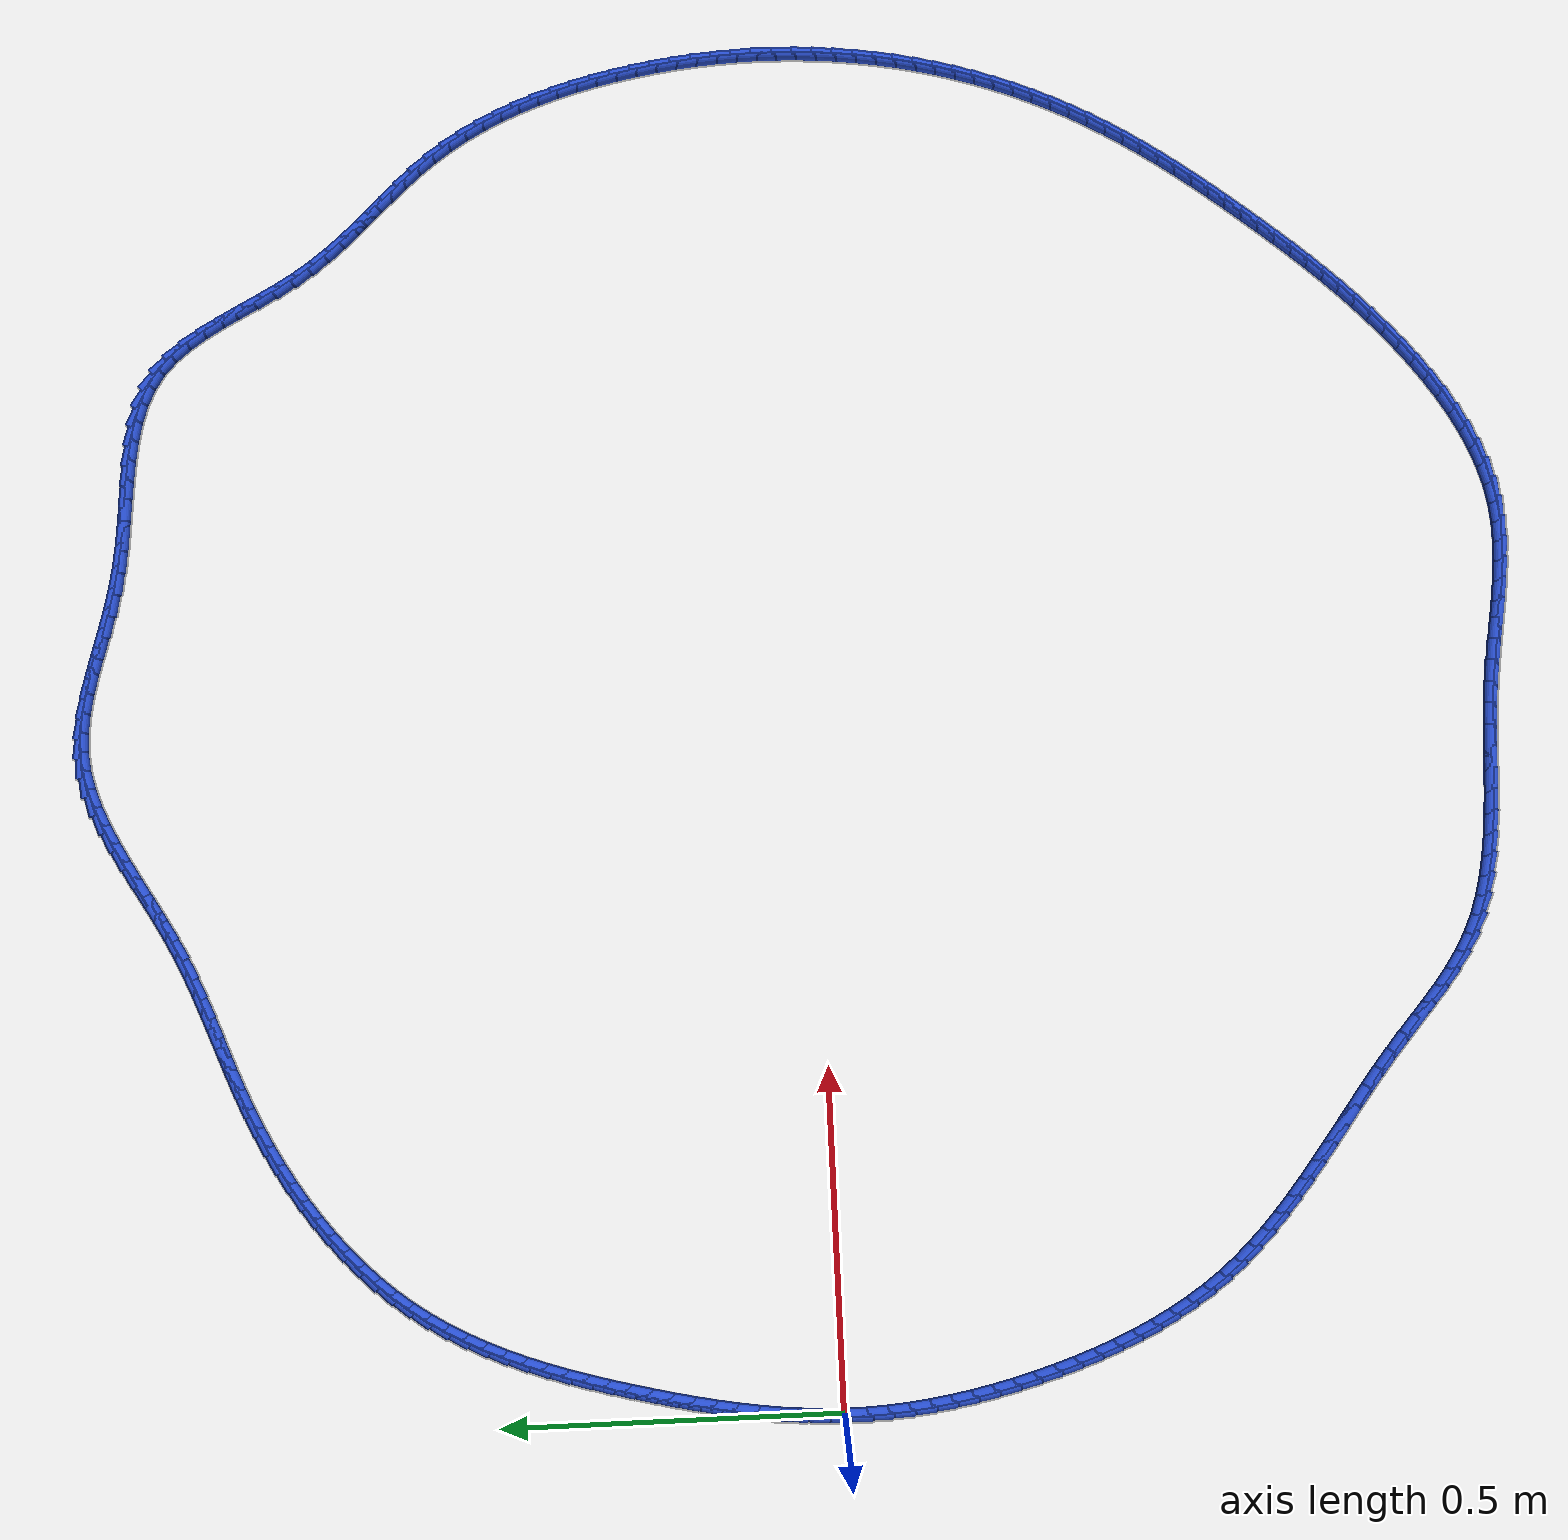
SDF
<sdf version="1.6">
 <world name="default">
  <light name="sun" type="directional">
   <pose>0 0 10 0 -0 0</pose>
   <diffuse>0.8 0.8 0.8 1</diffuse>
   <specular>0.2 0.2 0.2 1</specular>
   <attenuation>
    <range>1000</range>
    <constant>0.9</constant>
    <linear>0.01</linear>
    <quadratic>0.001</quadratic>
   </attenuation>
   <direction>-0.5 0.1 -0.9</direction>
  </light>
  <model name="ground_plane">
   <static>1</static>
   <link name="link">
    <collision name="collision">
     <geometry><plane><normal>0 0 1</normal><size>100 100</size></plane></geometry>
     <surface><friction><ode><mu>100</mu><mu2>50</mu2></ode></friction></surface>
    </collision>
    <visual name="visual">
     <cast_shadows>0</cast_shadows>
     <geometry><plane><normal>0 0 1</normal><size>100 100</size></plane></geometry>
     <material>
      <script><uri>file://media/materials/scripts/gazebo.material</uri><name>Gazebo/WhiteGlow</name></script>
     </material>
    </visual>
   </link>
  </model>
  <gravity>0 0 -9.8</gravity>
  <magnetic_field>6e-06 2.3e-05 -4.2e-05</magnetic_field>
  <atmosphere type="adiabatic"/>
  <physics name="default_physics" default="0" type="ode">
   <max_step_size>0.001</max_step_size>
   <real_time_factor>1</real_time_factor>
   <real_time_update_rate>1000</real_time_update_rate>
  </physics>
  <scene><ambient>0.4 0.4 0.4 1</ambient><background>0.7 0.7 0.7 1</background><shadows>1</shadows></scene>
  <spherical_coordinates>
   <surface_model>EARTH_WGS84</surface_model>
   <latitude_deg>0</latitude_deg>
   <longitude_deg>0</longitude_deg>
   <elevation>0</elevation>
   <heading_deg>0</heading_deg>
  </spherical_coordinates>
  <model name="line">
   <link name="link_0">
    <pose>1.734723475976807e-18 -4.85722573273506e-17 0.01 0 1.57 1.5412628216631568</pose>
    <collision name="collision">
     <geometry><cylinder><radius>0.01</radius><length>0.08</length></cylinder></geometry>
    </collision>
    <visual name="visual">
     <material>
      <script><name>Gazebo/Blue</name><uri>file://media/materials/scripts/gazebo.material</uri></script>
     </material>
     <geometry><cylinder><radius>0.01</radius><length>0.08</length></cylinder></geometry>
    </visual>
   </link>
   <link name="link_1">
    <pose>0.0009123240648302466 0.030882172428493955 0.01 0 1.57 1.5060534963203114</pose>
    <collision name="collision">
     <geometry><cylinder><radius>0.01</radius><length>0.08</length></cylinder></geometry>
    </collision>
    <visual name="visual">
     <material>
      <script><name>Gazebo/Blue</name><uri>file://media/materials/scripts/gazebo.material</uri></script>
     </material>
     <geometry><cylinder><radius>0.01</radius><length>0.08</length></cylinder></geometry>
    </visual>
   </link>
   <link name="link_2">
    <pose>0.002912517427017815 0.06173343230358804 0.01 0 1.57 1.473726464845135</pose>
    <collision name="collision">
     <geometry><cylinder><radius>0.01</radius><length>0.08</length></cylinder></geometry>
    </collision>
    <visual name="visual">
     <material>
      <script><name>Gazebo/Blue</name><uri>file://media/materials/scripts/gazebo.material</uri></script>
     </material>
     <geometry><cylinder><radius>0.01</radius><length>0.08</length></cylinder></geometry>
    </visual>
   </link>
   <link name="link_3">
    <pose>0.00591393406608708 0.09255642560275042 0.01 0 1.57 1.4443215227421433</pose>
    <collision name="collision">
     <geometry><cylinder><radius>0.01</radius><length>0.08</length></cylinder></geometry>
    </collision>
    <visual name="visual">
     <material>
      <script><name>Gazebo/Blue</name><uri>file://media/materials/scripts/gazebo.material</uri></script>
     </material>
     <geometry><cylinder><radius>0.01</radius><length>0.08</length></cylinder></geometry>
    </visual>
   </link>
   <link name="link_4">
    <pose>0.009829927961562424 0.12335379830344934 0.01 0 1.57 1.4178485512125907</pose>
    <collision name="collision">
     <geometry><cylinder><radius>0.01</radius><length>0.08</length></cylinder></geometry>
    </collision>
    <visual name="visual">
     <material>
      <script><name>Gazebo/Blue</name><uri>file://media/materials/scripts/gazebo.material</uri></script>
     </material>
     <geometry><cylinder><radius>0.01</radius><length>0.08</length></cylinder></geometry>
    </visual>
   </link>
   <link name="link_5">
    <pose>0.014573853092968216 0.15412819638315303 0.01 0 1.57 1.3942950668566918</pose>
    <collision name="collision">
     <geometry><cylinder><radius>0.01</radius><length>0.08</length></cylinder></geometry>
    </collision>
    <visual name="visual">
     <material>
      <script><name>Gazebo/Blue</name><uri>file://media/materials/scripts/gazebo.material</uri></script>
     </material>
     <geometry><cylinder><radius>0.01</radius><length>0.08</length></cylinder></geometry>
    </visual>
   </link>
   <link name="link_6">
    <pose>0.02005906343982885 0.18488226581932984 0.01 0 1.57 1.3736331449066561</pose>
    <collision name="collision">
     <geometry><cylinder><radius>0.01</radius><length>0.08</length></cylinder></geometry>
    </collision>
    <visual name="visual">
     <material>
      <script><name>Gazebo/Blue</name><uri>file://media/materials/scripts/gazebo.material</uri></script>
     </material>
     <geometry><cylinder><radius>0.01</radius><length>0.08</length></cylinder></geometry>
    </visual>
   </link>
   <link name="link_7">
    <pose>0.026198912981668696 0.215618652589448 0.01 0 1.57 1.3558254900949411</pose>
    <collision name="collision">
     <geometry><cylinder><radius>0.01</radius><length>0.08</length></cylinder></geometry>
    </collision>
    <visual name="visual">
     <material>
      <script><name>Gazebo/Blue</name><uri>file://media/materials/scripts/gazebo.material</uri></script>
     </material>
     <geometry><cylinder><radius>0.01</radius><length>0.08</length></cylinder></geometry>
    </visual>
   </link>
   <link name="link_8">
    <pose>0.032906755698012116 0.2463400026709756 0.01 0 1.57 1.3408305674102081</pose>
    <collision name="collision">
     <geometry><cylinder><radius>0.01</radius><length>0.08</length></cylinder></geometry>
    </collision>
    <visual name="visual">
     <material>
      <script><name>Gazebo/Blue</name><uri>file://media/materials/scripts/gazebo.material</uri></script>
     </material>
     <geometry><cylinder><radius>0.01</radius><length>0.08</length></cylinder></geometry>
    </visual>
   </link>
   <link name="link_9">
    <pose>0.0400959455683835 0.2770489620413811 0.01 0 1.57 1.3285257522312957</pose>
    <collision name="collision">
     <geometry><cylinder><radius>0.01</radius><length>0.08</length></cylinder></geometry>
    </collision>
    <visual name="visual">
     <material>
      <script><name>Gazebo/Blue</name><uri>file://media/materials/scripts/gazebo.material</uri></script>
     </material>
     <geometry><cylinder><radius>0.01</radius><length>0.08</length></cylinder></geometry>
    </visual>
   </link>
   <link name="link_10">
    <pose>0.04768220495748689 0.30774707758568953 0.01 0 1.57 1.3161149854434542</pose>
    <collision name="collision">
     <geometry><cylinder><radius>0.01</radius><length>0.08</length></cylinder></geometry>
    </collision>
    <visual name="visual">
     <material>
      <script><name>Gazebo/Blue</name><uri>file://media/materials/scripts/gazebo.material</uri></script>
     </material>
     <geometry><cylinder><radius>0.01</radius><length>0.08</length></cylinder></geometry>
    </visual>
   </link>
   <link name="link_11">
    <pose>0.05566182864192219 0.33839850508809877 0.01 0 1.57 1.3001817370770392</pose>
    <collision name="collision">
     <geometry><cylinder><radius>0.01</radius><length>0.08</length></cylinder></geometry>
    </collision>
    <visual name="visual">
     <material>
      <script><name>Gazebo/Blue</name><uri>file://media/materials/scripts/gazebo.material</uri></script>
     </material>
     <geometry><cylinder><radius>0.01</radius><length>0.08</length></cylinder></geometry>
    </visual>
   </link>
   <link name="link_12">
    <pose>0.06412957279832415 0.3689217075199748 0.01 0 1.57 1.280447265887555</pose>
    <collision name="collision">
     <geometry><cylinder><radius>0.01</radius><length>0.08</length></cylinder></geometry>
    </collision>
    <visual name="visual">
     <material>
      <script><name>Gazebo/Blue</name><uri>file://media/materials/scripts/gazebo.material</uri></script>
     </material>
     <geometry><cylinder><radius>0.01</radius><length>0.08</length></cylinder></geometry>
    </visual>
   </link>
   <link name="link_13">
    <pose>0.07318618493720835 0.39923236746465696 0.01 0 1.57 1.2568132840012687</pose>
    <collision name="collision">
     <geometry><cylinder><radius>0.01</radius><length>0.08</length></cylinder></geometry>
    </collision>
    <visual name="visual">
     <material>
      <script><name>Gazebo/Blue</name><uri>file://media/materials/scripts/gazebo.material</uri></script>
     </material>
     <geometry><cylinder><radius>0.01</radius><length>0.08</length></cylinder></geometry>
    </visual>
   </link>
   <link name="link_14">
    <pose>0.08293241256909038 0.42924616750548544 0.01 0 1.57 1.2291644485362587</pose>
    <collision name="collision">
     <geometry><cylinder><radius>0.01</radius><length>0.08</length></cylinder></geometry>
    </collision>
    <visual name="visual">
     <material>
      <script><name>Gazebo/Blue</name><uri>file://media/materials/scripts/gazebo.material</uri></script>
     </material>
     <geometry><cylinder><radius>0.01</radius><length>0.08</length></cylinder></geometry>
    </visual>
   </link>
   <link name="link_15">
    <pose>0.09346900320448578 0.45887879022580014 0.01 0 1.57 1.1973782347334503</pose>
    <collision name="collision">
     <geometry><cylinder><radius>0.01</radius><length>0.08</length></cylinder></geometry>
    </collision>
    <visual name="visual">
     <material>
      <script><name>Gazebo/Blue</name><uri>file://media/materials/scripts/gazebo.material</uri></script>
     </material>
     <geometry><cylinder><radius>0.01</radius><length>0.08</length></cylinder></geometry>
    </visual>
   </link>
   <link name="link_16">
    <pose>0.10489670435391017 0.4880459182089408 0.01 0 1.57 1.1613378274129564</pose>
    <collision name="collision">
     <geometry><cylinder><radius>0.01</radius><length>0.08</length></cylinder></geometry>
    </collision>
    <visual name="visual">
     <material>
      <script><name>Gazebo/Blue</name><uri>file://media/materials/scripts/gazebo.material</uri></script>
     </material>
     <geometry><cylinder><radius>0.01</radius><length>0.08</length></cylinder></geometry>
    </visual>
   </link>
   <link name="link_17">
    <pose>0.1173162635278791 0.5166632340382473 0.01 0 1.57 1.1209486049393367</pose>
    <collision name="collision">
     <geometry><cylinder><radius>0.01</radius><length>0.08</length></cylinder></geometry>
    </collision>
    <visual name="visual">
     <material>
      <script><name>Gazebo/Blue</name><uri>file://media/materials/scripts/gazebo.material</uri></script>
     </material>
     <geometry><cylinder><radius>0.01</radius><length>0.08</length></cylinder></geometry>
    </visual>
   </link>
   <link name="link_18">
    <pose>0.13082842823690818 0.5446464202970596 0.01 0 1.57 1.076158478595051</pose>
    <collision name="collision">
     <geometry><cylinder><radius>0.01</radius><length>0.08</length></cylinder></geometry>
    </collision>
    <visual name="visual">
     <material>
      <script><name>Gazebo/Blue</name><uri>file://media/materials/scripts/gazebo.material</uri></script>
     </material>
     <geometry><cylinder><radius>0.01</radius><length>0.08</length></cylinder></geometry>
    </visual>
   </link>
   <link name="link_19">
    <pose>0.14553394599151304 0.5719111595687173 0.01 0 1.57 1.0269817352253763</pose>
    <collision name="collision">
     <geometry><cylinder><radius>0.01</radius><length>0.08</length></cylinder></geometry>
    </collision>
    <visual name="visual">
     <material>
      <script><name>Gazebo/Blue</name><uri>file://media/materials/scripts/gazebo.material</uri></script>
     </material>
     <geometry><cylinder><radius>0.01</radius><length>0.08</length></cylinder></geometry>
    </visual>
   </link>
   <link name="link_20">
    <pose>0.16153356430220916 0.5983731344365608 0.01 0 1.57 0.9735250481433405</pose>
    <collision name="collision">
     <geometry><cylinder><radius>0.01</radius><length>0.08</length></cylinder></geometry>
    </collision>
    <visual name="visual">
     <material>
      <script><name>Gazebo/Blue</name><uri>file://media/materials/scripts/gazebo.material</uri></script>
     </material>
     <geometry><cylinder><radius>0.01</radius><length>0.08</length></cylinder></geometry>
    </visual>
   </link>
   <link name="link_21">
    <pose>0.17892803067951218 0.6239480274839294 0.01 0 1.57 0.9170099835365138</pose>
    <collision name="collision">
     <geometry><cylinder><radius>0.01</radius><length>0.08</length></cylinder></geometry>
    </collision>
    <visual name="visual">
     <material>
      <script><name>Gazebo/Blue</name><uri>file://media/materials/scripts/gazebo.material</uri></script>
     </material>
     <geometry><cylinder><radius>0.01</radius><length>0.08</length></cylinder></geometry>
    </visual>
   </link>
   <link name="link_22">
    <pose>0.19778789461691704 0.648562955459881 0.01 0 1.57 0.8622299062537365</pose>
    <collision name="collision">
     <geometry><cylinder><radius>0.01</radius><length>0.08</length></cylinder></geometry>
    </collision>
    <visual name="visual">
     <material>
      <script><name>Gazebo/Blue</name><uri>file://media/materials/scripts/gazebo.material</uri></script>
     </material>
     <geometry><cylinder><radius>0.01</radius><length>0.08</length></cylinder></geometry>
    </visual>
   </link>
   <link name="link_23">
    <pose>0.21804399486777634 0.6721979351351592 0.01 0 1.57 0.8104541867598475</pose>
    <collision name="collision">
     <geometry><cylinder><radius>0.01</radius><length>0.08</length></cylinder></geometry>
    </collision>
    <visual name="visual">
     <material>
      <script><name>Gazebo/Blue</name><uri>file://media/materials/scripts/gazebo.material</uri></script>
     </material>
     <geometry><cylinder><radius>0.01</radius><length>0.08</length></cylinder></geometry>
    </visual>
   </link>
   <link name="link_24">
    <pose>0.23958679473479041 0.6948482710258387 0.01 0 1.57 0.7615419906599273</pose>
    <collision name="collision">
     <geometry><cylinder><radius>0.01</radius><length>0.08</length></cylinder></geometry>
    </collision>
    <visual name="visual">
     <material>
      <script><name>Gazebo/Blue</name><uri>file://media/materials/scripts/gazebo.material</uri></script>
     </material>
     <geometry><cylinder><radius>0.01</radius><length>0.08</length></cylinder></geometry>
    </visual>
   </link>
   <link name="link_25">
    <pose>0.2623067535381841 0.716509269155916 0.01 0 1.57 0.7153153398035537</pose>
    <collision name="collision">
     <geometry><cylinder><radius>0.01</radius><length>0.08</length></cylinder></geometry>
    </collision>
    <visual name="visual">
     <material>
      <script><name>Gazebo/Blue</name><uri>file://media/materials/scripts/gazebo.material</uri></script>
     </material>
     <geometry><cylinder><radius>0.01</radius><length>0.08</length></cylinder></geometry>
    </visual>
   </link>
   <link name="link_26">
    <pose>0.28609433059818234 0.7371762355493882 0.01 0 1.57 0.6715719250338176</pose>
    <collision name="collision">
     <geometry><cylinder><radius>0.01</radius><length>0.08</length></cylinder></geometry>
    </collision>
    <visual name="visual">
     <material>
      <script><name>Gazebo/Blue</name><uri>file://media/materials/scripts/gazebo.material</uri></script>
     </material>
     <geometry><cylinder><radius>0.01</radius><length>0.08</length></cylinder></geometry>
    </visual>
   </link>
   <link name="link_27">
    <pose>0.3108399852350104 0.7568444762302526 0.01 0 1.57 0.6300948642467511</pose>
    <collision name="collision">
     <geometry><cylinder><radius>0.01</radius><length>0.08</length></cylinder></geometry>
    </collision>
    <visual name="visual">
     <material>
      <script><name>Gazebo/Blue</name><uri>file://media/materials/scripts/gazebo.material</uri></script>
     </material>
     <geometry><cylinder><radius>0.01</radius><length>0.08</length></cylinder></geometry>
    </visual>
   </link>
   <link name="link_28">
    <pose>0.33643417676889287 0.7755092972225057 0.01 0 1.57 0.5906597451188239</pose>
    <collision name="collision">
     <geometry><cylinder><radius>0.01</radius><length>0.08</length></cylinder></geometry>
    </collision>
    <visual name="visual">
     <material>
      <script><name>Gazebo/Blue</name><uri>file://media/materials/scripts/gazebo.material</uri></script>
     </material>
     <geometry><cylinder><radius>0.01</radius><length>0.08</length></cylinder></geometry>
    </visual>
   </link>
   <link name="link_29">
    <pose>0.3627673645200548 0.7931660045501447 0.01 0 1.57 0.5530393051871895</pose>
    <collision name="collision">
     <geometry><cylinder><radius>0.01</radius><length>0.08</length></cylinder></geometry>
    </collision>
    <visual name="visual">
     <material>
      <script><name>Gazebo/Blue</name><uri>file://media/materials/scripts/gazebo.material</uri></script>
     </material>
     <geometry><cylinder><radius>0.01</radius><length>0.08</length></cylinder></geometry>
    </visual>
   </link>
   <link name="link_30">
    <pose>0.38973000780872136 0.8098099042371668 0.01 0 1.57 0.5170061355439763</pose>
    <collision name="collision">
     <geometry><cylinder><radius>0.01</radius><length>0.08</length></cylinder></geometry>
    </collision>
    <visual name="visual">
     <material>
      <script><name>Gazebo/Blue</name><uri>file://media/materials/scripts/gazebo.material</uri></script>
     </material>
     <geometry><cylinder><radius>0.01</radius><length>0.08</length></cylinder></geometry>
    </visual>
   </link>
   <link name="link_31">
    <pose>0.41721256595511735 0.8254363023075686 0.01 0 1.57 0.4823337613582908</pose>
    <collision name="collision">
     <geometry><cylinder><radius>0.01</radius><length>0.08</length></cylinder></geometry>
    </collision>
    <visual name="visual">
     <material>
      <script><name>Gazebo/Blue</name><uri>file://media/materials/scripts/gazebo.material</uri></script>
     </material>
     <geometry><cylinder><radius>0.01</radius><length>0.08</length></cylinder></geometry>
    </visual>
   </link>
   <link name="link_32">
    <pose>0.44510549827946794 0.8400405047853473 0.01 0 1.57 0.44879773484372965</pose>
    <collision name="collision">
     <geometry><cylinder><radius>0.01</radius><length>0.08</length></cylinder></geometry>
    </collision>
    <visual name="visual">
     <material>
      <script><name>Gazebo/Blue</name><uri>file://media/materials/scripts/gazebo.material</uri></script>
     </material>
     <geometry><cylinder><radius>0.01</radius><length>0.08</length></cylinder></geometry>
    </visual>
   </link>
   <link name="link_33">
    <pose>0.4732992762979598 0.8536178704643717 0.01 0 1.57 0.41785313241853755</pose>
    <collision name="collision">
     <geometry><cylinder><radius>0.01</radius><length>0.08</length></cylinder></geometry>
    </collision>
    <visual name="visual">
     <material>
      <script><name>Gazebo/Blue</name><uri>file://media/materials/scripts/gazebo.material</uri></script>
     </material>
     <geometry><cylinder><radius>0.01</radius><length>0.08</length></cylinder></geometry>
    </visual>
   </link>
   <link name="link_34">
    <pose>0.5016990758842036 0.8662273814150796 0.01 0 1.57 0.39449636285148354</pose>
    <collision name="collision">
     <geometry><cylinder><radius>0.01</radius><length>0.08</length></cylinder></geometry>
    </collision>
    <visual name="visual">
     <material>
      <script><name>Gazebo/Blue</name><uri>file://media/materials/scripts/gazebo.material</uri></script>
     </material>
     <geometry><cylinder><radius>0.01</radius><length>0.08</length></cylinder></geometry>
    </visual>
   </link>
   <link name="link_35">
    <pose>0.5302533107953475 0.8781151027434528 0.01 0 1.57 0.3799111860514382</pose>
    <collision name="collision">
     <geometry><cylinder><radius>0.01</radius><length>0.08</length></cylinder></geometry>
    </collision>
    <visual name="visual">
     <material>
      <script><name>Gazebo/Blue</name><uri>file://media/materials/scripts/gazebo.material</uri></script>
     </material>
     <geometry><cylinder><radius>0.01</radius><length>0.08</length></cylinder></geometry>
    </visual>
   </link>
   <link name="link_36">
    <pose>0.5589183020704553 0.889561313031773 0.01 0 1.57 0.37425460069224775</pose>
    <collision name="collision">
     <geometry><cylinder><radius>0.01</radius><length>0.08</length></cylinder></geometry>
    </collision>
    <visual name="visual">
     <material>
      <script><name>Gazebo/Blue</name><uri>file://media/materials/scripts/gazebo.material</uri></script>
     </material>
     <geometry><cylinder><radius>0.01</radius><length>0.08</length></cylinder></geometry>
    </visual>
   </link>
   <link name="link_37">
    <pose>0.5876503707485907 0.9008462908623217 0.01 0 1.57 0.3775600619279605</pose>
    <collision name="collision">
     <geometry><cylinder><radius>0.01</radius><length>0.08</length></cylinder></geometry>
    </collision>
    <visual name="visual">
     <material>
      <script><name>Gazebo/Blue</name><uri>file://media/materials/scripts/gazebo.material</uri></script>
     </material>
     <geometry><cylinder><radius>0.01</radius><length>0.08</length></cylinder></geometry>
    </visual>
   </link>
   <link name="link_38">
    <pose>0.6164058378688172 0.9122503148173811 0.01 0 1.57 0.38975017043742327</pose>
    <collision name="collision">
     <geometry><cylinder><radius>0.01</radius><length>0.08</length></cylinder></geometry>
    </collision>
    <visual name="visual">
     <material>
      <script><name>Gazebo/Blue</name><uri>file://media/materials/scripts/gazebo.material</uri></script>
     </material>
     <geometry><cylinder><radius>0.01</radius><length>0.08</length></cylinder></geometry>
    </visual>
   </link>
   <link name="link_39">
    <pose>0.6451410244701985 0.9240536634792329 0.01 0 1.57 0.41063179023373153</pose>
    <collision name="collision">
     <geometry><cylinder><radius>0.01</radius><length>0.08</length></cylinder></geometry>
    </collision>
    <visual name="visual">
     <material>
      <script><name>Gazebo/Blue</name><uri>file://media/materials/scripts/gazebo.material</uri></script>
     </material>
     <geometry><cylinder><radius>0.01</radius><length>0.08</length></cylinder></geometry>
    </visual>
   </link>
   <link name="link_40">
    <pose>0.6738122515917987 0.9365366154301592 0.01 0 1.57 0.4398754014882249</pose>
    <collision name="collision">
     <geometry><cylinder><radius>0.01</radius><length>0.08</length></cylinder></geometry>
    </collision>
    <visual name="visual">
     <material>
      <script><name>Gazebo/Blue</name><uri>file://media/materials/scripts/gazebo.material</uri></script>
     </material>
     <geometry><cylinder><radius>0.01</radius><length>0.08</length></cylinder></geometry>
    </visual>
   </link>
   <link name="link_41">
    <pose>0.7023758402726813 0.9499794492524419 0.01 0 1.57 0.47686178427481807</pose>
    <collision name="collision">
     <geometry><cylinder><radius>0.01</radius><length>0.08</length></cylinder></geometry>
    </collision>
    <visual name="visual">
     <material>
      <script><name>Gazebo/Blue</name><uri>file://media/materials/scripts/gazebo.material</uri></script>
     </material>
     <geometry><cylinder><radius>0.01</radius><length>0.08</length></cylinder></geometry>
    </visual>
   </link>
   <link name="link_42">
    <pose>0.730788560513059 0.9646582718048161 0.01 0 1.57 0.5126657409627811</pose>
    <collision name="collision">
     <geometry><cylinder><radius>0.01</radius><length>0.08</length></cylinder></geometry>
    </collision>
    <visual name="visual">
     <material>
      <script><name>Gazebo/Blue</name><uri>file://media/materials/scripts/gazebo.material</uri></script>
     </material>
     <geometry><cylinder><radius>0.01</radius><length>0.08</length></cylinder></geometry>
    </visual>
   </link>
   <link name="link_43">
    <pose>0.7590384034824416 0.9805590844717675 0.01 0 1.57 0.5340961172704325</pose>
    <collision name="collision">
     <geometry><cylinder><radius>0.01</radius><length>0.08</length></cylinder></geometry>
    </collision>
    <visual name="visual">
     <material>
      <script><name>Gazebo/Blue</name><uri>file://media/materials/scripts/gazebo.material</uri></script>
     </material>
     <geometry><cylinder><radius>0.01</radius><length>0.08</length></cylinder></geometry>
    </visual>
   </link>
   <link name="link_44">
    <pose>0.7871643914444696 0.9971937103767368 0.01 0 1.57 0.5406539949797214</pose>
    <collision name="collision">
     <geometry><cylinder><radius>0.01</radius><length>0.08</length></cylinder></geometry>
    </collision>
    <visual name="visual">
     <material>
      <script><name>Gazebo/Blue</name><uri>file://media/materials/scripts/gazebo.material</uri></script>
     </material>
     <geometry><cylinder><radius>0.01</radius><length>0.08</length></cylinder></geometry>
    </visual>
   </link>
   <link name="link_45">
    <pose>0.8152102599600243 1.0140301769314102 0.01 0 1.57 0.532523852663507</pose>
    <collision name="collision">
     <geometry><cylinder><radius>0.01</radius><length>0.08</length></cylinder></geometry>
    </collision>
    <visual name="visual">
     <material>
      <script><name>Gazebo/Blue</name><uri>file://media/materials/scripts/gazebo.material</uri></script>
     </material>
     <geometry><cylinder><radius>0.01</radius><length>0.08</length></cylinder></geometry>
    </visual>
   </link>
   <link name="link_46">
    <pose>0.8432197445899874 1.0305365115474745 0.01 0 1.57 0.5092593615520646</pose>
    <collision name="collision">
     <geometry><cylinder><radius>0.01</radius><length>0.08</length></cylinder></geometry>
    </collision>
    <visual name="visual">
     <material>
      <script><name>Gazebo/Blue</name><uri>file://media/materials/scripts/gazebo.material</uri></script>
     </material>
     <geometry><cylinder><radius>0.01</radius><length>0.08</length></cylinder></geometry>
    </visual>
   </link>
   <link name="link_47">
    <pose>0.8712365808952395 1.046180741636616 0.01 0 1.57 0.46979054889330396</pose>
    <collision name="collision">
     <geometry><cylinder><radius>0.01</radius><length>0.08</length></cylinder></geometry>
    </collision>
    <visual name="visual">
     <material>
      <script><name>Gazebo/Blue</name><uri>file://media/materials/scripts/gazebo.material</uri></script>
     </material>
     <geometry><cylinder><radius>0.01</radius><length>0.08</length></cylinder></geometry>
    </visual>
   </link>
   <link name="link_48">
    <pose>0.8993045044366627 1.0604308946105216 0.01 0 1.57 0.41249692012261846</pose>
    <collision name="collision">
     <geometry><cylinder><radius>0.01</radius><length>0.08</length></cylinder></geometry>
    </collision>
    <visual name="visual">
     <material>
      <script><name>Gazebo/Blue</name><uri>file://media/materials/scripts/gazebo.material</uri></script>
     </material>
     <geometry><cylinder><radius>0.01</radius><length>0.08</length></cylinder></geometry>
    </visual>
   </link>
   <link name="link_49">
    <pose>0.927467250775138 1.0727549978808772 0.01 0 1.57 0.3354348147227649</pose>
    <collision name="collision">
     <geometry><cylinder><radius>0.01</radius><length>0.08</length></cylinder></geometry>
    </collision>
    <visual name="visual">
     <material>
      <script><name>Gazebo/Blue</name><uri>file://media/materials/scripts/gazebo.material</uri></script>
     </material>
     <geometry><cylinder><radius>0.01</radius><length>0.08</length></cylinder></geometry>
    </visual>
   </link>
   <link name="link_50">
    <pose>0.955768555471546 1.0826210788593689 0.01 0 1.57 0.2368731347670547</pose>
    <collision name="collision">
     <geometry><cylinder><radius>0.01</radius><length>0.08</length></cylinder></geometry>
    </collision>
    <visual name="visual">
     <material>
      <script><name>Gazebo/Blue</name><uri>file://media/materials/scripts/gazebo.material</uri></script>
     </material>
     <geometry><cylinder><radius>0.01</radius><length>0.08</length></cylinder></geometry>
    </visual>
   </link>
   <link name="link_51">
    <pose>0.9842521540867695 1.0894971649576841 0.01 0 1.57 0.11640558924391527</pose>
    <collision name="collision">
     <geometry><cylinder><radius>0.01</radius><length>0.08</length></cylinder></geometry>
    </collision>
    <visual name="visual">
     <material>
      <script><name>Gazebo/Blue</name><uri>file://media/materials/scripts/gazebo.material</uri></script>
     </material>
     <geometry><cylinder><radius>0.01</radius><length>0.08</length></cylinder></geometry>
    </visual>
   </link>
   <link name="link_52">
    <pose>1.0129617833352642 1.0928543033502458 0.01 0 1.57 -0.010875138252583438</pose>
    <collision name="collision">
     <geometry><cylinder><radius>0.01</radius><length>0.08</length></cylinder></geometry>
    </collision>
    <visual name="visual">
     <material>
      <script><name>Gazebo/Blue</name><uri>file://media/materials/scripts/gazebo.material</uri></script>
     </material>
     <geometry><cylinder><radius>0.01</radius><length>0.08</length></cylinder></geometry>
    </visual>
   </link>
   <link name="link_53">
    <pose>1.0419413234114148 1.0925391344204574 0.01 0 1.57 -0.11574545926502423</pose>
    <collision name="collision">
     <geometry><cylinder><radius>0.01</radius><length>0.08</length></cylinder></geometry>
    </collision>
    <visual name="visual">
     <material>
      <script><name>Gazebo/Blue</name><uri>file://media/materials/scripts/gazebo.material</uri></script>
     </material>
     <geometry><cylinder><radius>0.01</radius><length>0.08</length></cylinder></geometry>
    </visual>
   </link>
   <link name="link_54">
    <pose>1.0712349352900807 1.0891333089646507 0.01 0 1.57 -0.1941256304616018</pose>
    <collision name="collision">
     <geometry><cylinder><radius>0.01</radius><length>0.08</length></cylinder></geometry>
    </collision>
    <visual name="visual">
     <material>
      <script><name>Gazebo/Blue</name><uri>file://media/materials/scripts/gazebo.material</uri></script>
     </material>
     <geometry><cylinder><radius>0.01</radius><length>0.08</length></cylinder></geometry>
    </visual>
   </link>
   <link name="link_55">
    <pose>1.1008868125040177 1.0833037059038246 0.01 0 1.57 -0.24726083537759808</pose>
    <collision name="collision">
     <geometry><cylinder><radius>0.01</radius><length>0.08</length></cylinder></geometry>
    </collision>
    <visual name="visual">
     <material>
      <script><name>Gazebo/Blue</name><uri>file://media/materials/scripts/gazebo.material</uri></script>
     </material>
     <geometry><cylinder><radius>0.01</radius><length>0.08</length></cylinder></geometry>
    </visual>
   </link>
   <link name="link_56">
    <pose>1.1309411485859837 1.0757172041589793 0.01 0 1.57 -0.27714603197713644</pose>
    <collision name="collision">
     <geometry><cylinder><radius>0.01</radius><length>0.08</length></cylinder></geometry>
    </collision>
    <visual name="visual">
     <material>
      <script><name>Gazebo/Blue</name><uri>file://media/materials/scripts/gazebo.material</uri></script>
     </material>
     <geometry><cylinder><radius>0.01</radius><length>0.08</length></cylinder></geometry>
    </visual>
   </link>
   <link name="link_57">
    <pose>1.1614421370687338 1.067040682651114 0.01 0 1.57 -0.28558859954213506</pose>
    <collision name="collision">
     <geometry><cylinder><radius>0.01</radius><length>0.08</length></cylinder></geometry>
    </collision>
    <visual name="visual">
     <material>
      <script><name>Gazebo/Blue</name><uri>file://media/materials/scripts/gazebo.material</uri></script>
     </material>
     <geometry><cylinder><radius>0.01</radius><length>0.08</length></cylinder></geometry>
    </visual>
   </link>
   <link name="link_58">
    <pose>1.1924339714850254 1.0579410203012292 0.01 0 1.57 -0.2738438243102279</pose>
    <collision name="collision">
     <geometry><cylinder><radius>0.01</radius><length>0.08</length></cylinder></geometry>
    </collision>
    <visual name="visual">
     <material>
      <script><name>Gazebo/Blue</name><uri>file://media/materials/scripts/gazebo.material</uri></script>
     </material>
     <geometry><cylinder><radius>0.01</radius><length>0.08</length></cylinder></geometry>
    </visual>
   </link>
   <link name="link_59">
    <pose>1.2239608453676154 1.0490850960303237 0.01 0 1.57 -0.2425963369911499</pose>
    <collision name="collision">
     <geometry><cylinder><radius>0.01</radius><length>0.08</length></cylinder></geometry>
    </collision>
    <visual name="visual">
     <material>
      <script><name>Gazebo/Blue</name><uri>file://media/materials/scripts/gazebo.material</uri></script>
     </material>
     <geometry><cylinder><radius>0.01</radius><length>0.08</length></cylinder></geometry>
    </visual>
   </link>
   <link name="link_60">
    <pose>1.25606695224926 1.0411397887593978 0.01 0 1.57 -0.1925973241402609</pose>
    <collision name="collision">
     <geometry><cylinder><radius>0.01</radius><length>0.08</length></cylinder></geometry>
    </collision>
    <visual name="visual">
     <material>
      <script><name>Gazebo/Blue</name><uri>file://media/materials/scripts/gazebo.material</uri></script>
     </material>
     <geometry><cylinder><radius>0.01</radius><length>0.08</length></cylinder></geometry>
    </visual>
   </link>
   <link name="link_61">
    <pose>1.2887923483782944 1.0347578593502977 0.01 0 1.57 -0.14027515189939124</pose>
    <collision name="collision">
     <geometry><cylinder><radius>0.01</radius><length>0.08</length></cylinder></geometry>
    </collision>
    <visual name="visual">
     <material>
      <script><name>Gazebo/Blue</name><uri>file://media/materials/scripts/gazebo.material</uri></script>
     </material>
     <geometry><cylinder><radius>0.01</radius><length>0.08</length></cylinder></geometry>
    </visual>
   </link>
   <link name="link_62">
    <pose>1.322022818554243 1.0300656331534572 0.01 0 1.57 -0.10573457963106597</pose>
    <collision name="collision">
     <geometry><cylinder><radius>0.01</radius><length>0.08</length></cylinder></geometry>
    </collision>
    <visual name="visual">
     <material>
      <script><name>Gazebo/Blue</name><uri>file://media/materials/scripts/gazebo.material</uri></script>
     </material>
     <geometry><cylinder><radius>0.01</radius><length>0.08</length></cylinder></geometry>
    </visual>
   </link>
   <link name="link_63">
    <pose>1.355447461116745 1.026518263128727 0.01 0 1.57 -0.08959134638462439</pose>
    <collision name="collision">
     <geometry><cylinder><radius>0.01</radius><length>0.08</length></cylinder></geometry>
    </collision>
    <visual name="visual">
     <material>
      <script><name>Gazebo/Blue</name><uri>file://media/materials/scripts/gazebo.material</uri></script>
     </material>
     <geometry><cylinder><radius>0.01</radius><length>0.08</length></cylinder></geometry>
    </visual>
   </link>
   <link name="link_64">
    <pose>1.388742596917879 1.0235273003689285 0.01 0 1.57 -0.09178839639875379</pose>
    <collision name="collision">
     <geometry><cylinder><radius>0.01</radius><length>0.08</length></cylinder></geometry>
    </collision>
    <visual name="visual">
     <material>
      <script><name>Gazebo/Blue</name><uri>file://media/materials/scripts/gazebo.material</uri></script>
     </material>
     <geometry><cylinder><radius>0.01</radius><length>0.08</length></cylinder></geometry>
    </visual>
   </link>
   <link name="link_65">
    <pose>1.4215845468097257 1.0205042959668826 0.01 0 1.57 -0.11314283208271267</pose>
    <collision name="collision">
     <geometry><cylinder><radius>0.01</radius><length>0.08</length></cylinder></geometry>
    </collision>
    <visual name="visual">
     <material>
      <script><name>Gazebo/Blue</name><uri>file://media/materials/scripts/gazebo.material</uri></script>
     </material>
     <geometry><cylinder><radius>0.01</radius><length>0.08</length></cylinder></geometry>
    </visual>
   </link>
   <link name="link_66">
    <pose>1.4536496316443654 1.01686080101541 0.01 0 1.57 -0.15544515642646436</pose>
    <collision name="collision">
     <geometry><cylinder><radius>0.01</radius><length>0.08</length></cylinder></geometry>
    </collision>
    <visual name="visual">
     <material>
      <script><name>Gazebo/Blue</name><uri>file://media/materials/scripts/gazebo.material</uri></script>
     </material>
     <geometry><cylinder><radius>0.01</radius><length>0.08</length></cylinder></geometry>
    </visual>
   </link>
   <link name="link_67">
    <pose>1.4846141722738768 1.0120083666073318 0.01 0 1.57 -0.22141920228450743</pose>
    <collision name="collision">
     <geometry><cylinder><radius>0.01</radius><length>0.08</length></cylinder></geometry>
    </collision>
    <visual name="visual">
     <material>
      <script><name>Gazebo/Blue</name><uri>file://media/materials/scripts/gazebo.material</uri></script>
     </material>
     <geometry><cylinder><radius>0.01</radius><length>0.08</length></cylinder></geometry>
    </visual>
   </link>
   <link name="link_68">
    <pose>1.5141544895503405 1.0053585438354693 0.01 0 1.57 -0.31433360237254365</pose>
    <collision name="collision">
     <geometry><cylinder><radius>0.01</radius><length>0.08</length></cylinder></geometry>
    </collision>
    <visual name="visual">
     <material>
      <script><name>Gazebo/Blue</name><uri>file://media/materials/scripts/gazebo.material</uri></script>
     </material>
     <geometry><cylinder><radius>0.01</radius><length>0.08</length></cylinder></geometry>
    </visual>
   </link>
   <link name="link_69">
    <pose>1.5419469043258363 0.9963228837926429 0.01 0 1.57 -0.4368471329134506</pose>
    <collision name="collision">
     <geometry><cylinder><radius>0.01</radius><length>0.08</length></cylinder></geometry>
    </collision>
    <visual name="visual">
     <material>
      <script><name>Gazebo/Blue</name><uri>file://media/materials/scripts/gazebo.material</uri></script>
     </material>
     <geometry><cylinder><radius>0.01</radius><length>0.08</length></cylinder></geometry>
    </visual>
   </link>
   <link name="link_70">
    <pose>1.567667737452443 0.9843129375716735 0.01 0 1.57 -0.5886170190808162</pose>
    <collision name="collision">
     <geometry><cylinder><radius>0.01</radius><length>0.08</length></cylinder></geometry>
    </collision>
    <visual name="visual">
     <material>
      <script><name>Gazebo/Blue</name><uri>file://media/materials/scripts/gazebo.material</uri></script>
     </material>
     <geometry><cylinder><radius>0.01</radius><length>0.08</length></cylinder></geometry>
    </visual>
   </link>
   <link name="link_71">
    <pose>1.5909940301017556 0.9687413654891458 0.01 0 1.57 -0.7495813461957737</pose>
    <collision name="collision">
     <geometry><cylinder><radius>0.01</radius><length>0.08</length></cylinder></geometry>
    </collision>
    <visual name="visual">
     <material>
      <script><name>Gazebo/Blue</name><uri>file://media/materials/scripts/gazebo.material</uri></script>
     </material>
     <geometry><cylinder><radius>0.01</radius><length>0.08</length></cylinder></geometry>
    </visual>
   </link>
   <link name="link_72">
    <pose>1.6118203990244238 0.9493558736266141 0.01 0 1.57 -0.8794598634114384</pose>
    <collision name="collision">
     <geometry><cylinder><radius>0.01</radius><length>0.08</length></cylinder></geometry>
    </collision>
    <visual name="visual">
     <material>
      <script><name>Gazebo/Blue</name><uri>file://media/materials/scripts/gazebo.material</uri></script>
     </material>
     <geometry><cylinder><radius>0.01</radius><length>0.08</length></cylinder></geometry>
    </visual>
   </link>
   <link name="link_73">
    <pose>1.6305634562664657 0.9267079913338813 0.01 0 1.57 -0.9739080413530348</pose>
    <collision name="collision">
     <geometry><cylinder><radius>0.01</radius><length>0.08</length></cylinder></geometry>
    </collision>
    <visual name="visual">
     <material>
      <script><name>Gazebo/Blue</name><uri>file://media/materials/scripts/gazebo.material</uri></script>
     </material>
     <geometry><cylinder><radius>0.01</radius><length>0.08</length></cylinder></geometry>
    </visual>
   </link>
   <link name="link_74">
    <pose>1.647716479812898 0.9014673062386637 0.01 0 1.57 -1.0369552021018358</pose>
    <collision name="collision">
     <geometry><cylinder><radius>0.01</radius><length>0.08</length></cylinder></geometry>
    </collision>
    <visual name="visual">
     <material>
      <script><name>Gazebo/Blue</name><uri>file://media/materials/scripts/gazebo.material</uri></script>
     </material>
     <geometry><cylinder><radius>0.01</radius><length>0.08</length></cylinder></geometry>
    </visual>
   </link>
   <link name="link_75">
    <pose>1.6637727476487396 0.8743034059686773 0.01 0 1.57 -1.0727436170641291</pose>
    <collision name="collision">
     <geometry><cylinder><radius>0.01</radius><length>0.08</length></cylinder></geometry>
    </collision>
    <visual name="visual">
     <material>
      <script><name>Gazebo/Blue</name><uri>file://media/materials/scripts/gazebo.material</uri></script>
     </material>
     <geometry><cylinder><radius>0.01</radius><length>0.08</length></cylinder></geometry>
    </visual>
   </link>
   <link name="link_76">
    <pose>1.6792255377590075 0.8458858781516372 0.01 0 1.57 -1.0841982680709366</pose>
    <collision name="collision">
     <geometry><cylinder><radius>0.01</radius><length>0.08</length></cylinder></geometry>
    </collision>
    <visual name="visual">
     <material>
      <script><name>Gazebo/Blue</name><uri>file://media/materials/scripts/gazebo.material</uri></script>
     </material>
     <geometry><cylinder><radius>0.01</radius><length>0.08</length></cylinder></geometry>
    </visual>
   </link>
   <link name="link_77">
    <pose>1.6945681281287193 0.8168843104152604 0.01 0 1.57 -1.0726953070698326</pose>
    <collision name="collision">
     <geometry><cylinder><radius>0.01</radius><length>0.08</length></cylinder></geometry>
    </collision>
    <visual name="visual">
     <material>
      <script><name>Gazebo/Blue</name><uri>file://media/materials/scripts/gazebo.material</uri></script>
     </material>
     <geometry><cylinder><radius>0.01</radius><length>0.08</length></cylinder></geometry>
    </visual>
   </link>
   <link name="link_78">
    <pose>1.7102937967428935 0.7879682903872625 0.01 0 1.57 -1.0381020073517435</pose>
    <collision name="collision">
     <geometry><cylinder><radius>0.01</radius><length>0.08</length></cylinder></geometry>
    </collision>
    <visual name="visual">
     <material>
      <script><name>Gazebo/Blue</name><uri>file://media/materials/scripts/gazebo.material</uri></script>
     </material>
     <geometry><cylinder><radius>0.01</radius><length>0.08</length></cylinder></geometry>
    </visual>
   </link>
   <link name="link_79">
    <pose>1.7268958215865458 0.7598074056953584 0.01 0 1.57 -0.9800896787414805</pose>
    <collision name="collision">
     <geometry><cylinder><radius>0.01</radius><length>0.08</length></cylinder></geometry>
    </collision>
    <visual name="visual">
     <material>
      <script><name>Gazebo/Blue</name><uri>file://media/materials/scripts/gazebo.material</uri></script>
     </material>
     <geometry><cylinder><radius>0.01</radius><length>0.08</length></cylinder></geometry>
    </visual>
   </link>
   <link name="link_80">
    <pose>1.7448435739711317 0.7330428677751545 0.01 0 1.57 -0.9172358337113629</pose>
    <collision name="collision">
     <geometry><cylinder><radius>0.01</radius><length>0.08</length></cylinder></geometry>
    </collision>
    <visual name="visual">
     <material>
      <script><name>Gazebo/Blue</name><uri>file://media/materials/scripts/gazebo.material</uri></script>
     </material>
     <geometry><cylinder><radius>0.01</radius><length>0.08</length></cylinder></geometry>
    </visual>
   </link>
   <link name="link_81">
    <pose>1.7641737441835172 0.7078023143171037 0.01 0 1.57 -0.8676791812387569</pose>
    <collision name="collision">
     <geometry><cylinder><radius>0.01</radius><length>0.08</length></cylinder></geometry>
    </collision>
    <visual name="visual">
     <material>
      <script><name>Gazebo/Blue</name><uri>file://media/materials/scripts/gazebo.material</uri></script>
     </material>
     <geometry><cylinder><radius>0.01</radius><length>0.08</length></cylinder></geometry>
    </visual>
   </link>
   <link name="link_82">
    <pose>1.7845468859056632 0.6837669250578925 0.01 0 1.57 -0.8328386760986537</pose>
    <collision name="collision">
     <geometry><cylinder><radius>0.01</radius><length>0.08</length></cylinder></geometry>
    </collision>
    <visual name="visual">
     <material>
      <script><name>Gazebo/Blue</name><uri>file://media/materials/scripts/gazebo.material</uri></script>
     </material>
     <geometry><cylinder><radius>0.01</radius><length>0.08</length></cylinder></geometry>
    </visual>
   </link>
   <link name="link_83">
    <pose>1.8056110246071904 0.6606030092856193 0.01 0 1.57 -0.8131673452226066</pose>
    <collision name="collision">
     <geometry><cylinder><radius>0.01</radius><length>0.08</length></cylinder></geometry>
    </collision>
    <visual name="visual">
     <material>
      <script><name>Gazebo/Blue</name><uri>file://media/materials/scripts/gazebo.material</uri></script>
     </material>
     <geometry><cylinder><radius>0.01</radius><length>0.08</length></cylinder></geometry>
    </visual>
   </link>
   <link name="link_84">
    <pose>1.827014185757719 0.6379768762883821 0.01 0 1.57 -0.8089450288613933</pose>
    <collision name="collision">
     <geometry><cylinder><radius>0.01</radius><length>0.08</length></cylinder></geometry>
    </collision>
    <visual name="visual">
     <material>
      <script><name>Gazebo/Blue</name><uri>file://media/materials/scripts/gazebo.material</uri></script>
     </material>
     <geometry><cylinder><radius>0.01</radius><length>0.08</length></cylinder></geometry>
    </visual>
   </link>
   <link name="link_85">
    <pose>1.8484043948268711 0.6155548353542791 0.01 0 1.57 -0.8204105804810243</pose>
    <collision name="collision">
     <geometry><cylinder><radius>0.01</radius><length>0.08</length></cylinder></geometry>
    </collision>
    <visual name="visual">
     <material>
      <script><name>Gazebo/Blue</name><uri>file://media/materials/scripts/gazebo.material</uri></script>
     </material>
     <geometry><cylinder><radius>0.01</radius><length>0.08</length></cylinder></geometry>
    </visual>
   </link>
   <link name="link_86">
    <pose>1.8694296772842656 0.5930031957714087 0.01 0 1.57 -0.8477903190574437</pose>
    <collision name="collision">
     <geometry><cylinder><radius>0.01</radius><length>0.08</length></cylinder></geometry>
    </collision>
    <visual name="visual">
     <material>
      <script><name>Gazebo/Blue</name><uri>file://media/materials/scripts/gazebo.material</uri></script>
     </material>
     <geometry><cylinder><radius>0.01</radius><length>0.08</length></cylinder></geometry>
    </visual>
   </link>
   <link name="link_87">
    <pose>1.8897380585995243 0.5699882668278689 0.01 0 1.57 -0.8912094683341767</pose>
    <collision name="collision">
     <geometry><cylinder><radius>0.01</radius><length>0.08</length></cylinder></geometry>
    </collision>
    <visual name="visual">
     <material>
      <script><name>Gazebo/Blue</name><uri>file://media/materials/scripts/gazebo.material</uri></script>
     </material>
     <geometry><cylinder><radius>0.01</radius><length>0.08</length></cylinder></geometry>
    </visual>
   </link>
   <link name="link_88">
    <pose>1.9089775642422677 0.5461763578117578 0.01 0 1.57 -0.9491147296151927</pose>
    <collision name="collision">
     <geometry><cylinder><radius>0.01</radius><length>0.08</length></cylinder></geometry>
    </collision>
    <visual name="visual">
     <material>
      <script><name>Gazebo/Blue</name><uri>file://media/materials/scripts/gazebo.material</uri></script>
     </material>
     <geometry><cylinder><radius>0.01</radius><length>0.08</length></cylinder></geometry>
    </visual>
   </link>
   <link name="link_89">
    <pose>1.9268253142343728 0.5212650139772419 0.01 0 1.57 -1.0091416666556263</pose>
    <collision name="collision">
     <geometry><cylinder><radius>0.01</radius><length>0.08</length></cylinder></geometry>
    </collision>
    <visual name="visual">
     <material>
      <script><name>Gazebo/Blue</name><uri>file://media/materials/scripts/gazebo.material</uri></script>
     </material>
     <geometry><cylinder><radius>0.01</radius><length>0.08</length></cylinder></geometry>
    </visual>
   </link>
   <link name="link_90">
    <pose>1.9432118773200204 0.4952238836038323 0.01 0 1.57 -1.065036971241502</pose>
    <collision name="collision">
     <geometry><cylinder><radius>0.01</radius><length>0.08</length></cylinder></geometry>
    </collision>
    <visual name="visual">
     <material>
      <script><name>Gazebo/Blue</name><uri>file://media/materials/scripts/gazebo.material</uri></script>
     </material>
     <geometry><cylinder><radius>0.01</radius><length>0.08</length></cylinder></geometry>
    </visual>
   </link>
   <link name="link_91">
    <pose>1.9581984139895385 0.46816281851552105 0.01 0 1.57 -1.1168120620067408</pose>
    <collision name="collision">
     <geometry><cylinder><radius>0.01</radius><length>0.08</length></cylinder></geometry>
    </collision>
    <visual name="visual">
     <material>
      <script><name>Gazebo/Blue</name><uri>file://media/materials/scripts/gazebo.material</uri></script>
     </material>
     <geometry><cylinder><radius>0.01</radius><length>0.08</length></cylinder></geometry>
    </visual>
   </link>
   <link name="link_92">
    <pose>1.971847166770858 0.4401928322139081 0.01 0 1.57 -1.1646097633688304</pose>
    <collision name="collision">
     <geometry><cylinder><radius>0.01</radius><length>0.08</length></cylinder></geometry>
    </collision>
    <visual name="visual">
     <material>
      <script><name>Gazebo/Blue</name><uri>file://media/materials/scripts/gazebo.material</uri></script>
     </material>
     <geometry><cylinder><radius>0.01</radius><length>0.08</length></cylinder></geometry>
    </visual>
   </link>
   <link name="link_93">
    <pose>1.98422037819191 0.4114249382005948 0.01 0 1.57 -1.208625912299175</pose>
    <collision name="collision">
     <geometry><cylinder><radius>0.01</radius><length>0.08</length></cylinder></geometry>
    </collision>
    <visual name="visual">
     <material>
      <script><name>Gazebo/Blue</name><uri>file://media/materials/scripts/gazebo.material</uri></script>
     </material>
     <geometry><cylinder><radius>0.01</radius><length>0.08</length></cylinder></geometry>
    </visual>
   </link>
   <link name="link_94">
    <pose>1.9953802907806253 0.38197014997718104 0.01 0 1.57 -1.2490867318750942</pose>
    <collision name="collision">
     <geometry><cylinder><radius>0.01</radius><length>0.08</length></cylinder></geometry>
    </collision>
    <visual name="visual">
     <material>
      <script><name>Gazebo/Blue</name><uri>file://media/materials/scripts/gazebo.material</uri></script>
     </material>
     <geometry><cylinder><radius>0.01</radius><length>0.08</length></cylinder></geometry>
    </visual>
   </link>
   <link name="link_95">
    <pose>2.005389147064935 0.3519394810452667 0.01 0 1.57 -1.2862314237658226</pose>
    <collision name="collision">
     <geometry><cylinder><radius>0.01</radius><length>0.08</length></cylinder></geometry>
    </collision>
    <visual name="visual">
     <material>
      <script><name>Gazebo/Blue</name><uri>file://media/materials/scripts/gazebo.material</uri></script>
     </material>
     <geometry><cylinder><radius>0.01</radius><length>0.08</length></cylinder></geometry>
    </visual>
   </link>
   <link name="link_96">
    <pose>2.0143091895727707 0.32144394490645306 0.01 0 1.57 -1.3202994813837805</pose>
    <collision name="collision">
     <geometry><cylinder><radius>0.01</radius><length>0.08</length></cylinder></geometry>
    </collision>
    <visual name="visual">
     <material>
      <script><name>Gazebo/Blue</name><uri>file://media/materials/scripts/gazebo.material</uri></script>
     </material>
     <geometry><cylinder><radius>0.01</radius><length>0.08</length></cylinder></geometry>
    </visual>
   </link>
   <link name="link_97">
    <pose>2.0222026608320633 0.2905945550623401 0.01 0 1.57 -1.3515218998815273</pose>
    <collision name="collision">
     <geometry><cylinder><radius>0.01</radius><length>0.08</length></cylinder></geometry>
    </collision>
    <visual name="visual">
     <material>
      <script><name>Gazebo/Blue</name><uri>file://media/materials/scripts/gazebo.material</uri></script>
     </material>
     <geometry><cylinder><radius>0.01</radius><length>0.08</length></cylinder></geometry>
    </visual>
   </link>
   <link name="link_98">
    <pose>2.029131803370743 0.25950232501452786 0.01 0 1.57 -1.3802130893798659</pose>
    <collision name="collision">
     <geometry><cylinder><radius>0.01</radius><length>0.08</length></cylinder></geometry>
    </collision>
    <visual name="visual">
     <material>
      <script><name>Gazebo/Blue</name><uri>file://media/materials/scripts/gazebo.material</uri></script>
     </material>
     <geometry><cylinder><radius>0.01</radius><length>0.08</length></cylinder></geometry>
    </visual>
   </link>
   <link name="link_99">
    <pose>2.0351563592875737 0.2282748282394207 0.01 0 1.57 -1.4079384231233527</pose>
    <collision name="collision">
     <geometry><cylinder><radius>0.01</radius><length>0.08</length></cylinder></geometry>
    </collision>
    <visual name="visual">
     <material>
      <script><name>Gazebo/Blue</name><uri>file://media/materials/scripts/gazebo.material</uri></script>
     </material>
     <geometry><cylinder><radius>0.01</radius><length>0.08</length></cylinder></geometry>
    </visual>
   </link>
   <link name="link_100">
    <pose>2.0403001241544647 0.19697018391986434 0.01 0 1.57 -1.4357893926437775</pose>
    <collision name="collision">
     <geometry><cylinder><radius>0.01</radius><length>0.08</length></cylinder></geometry>
    </collision>
    <visual name="visual">
     <material>
      <script><name>Gazebo/Blue</name><uri>file://media/materials/scripts/gazebo.material</uri></script>
     </material>
     <geometry><cylinder><radius>0.01</radius><length>0.08</length></cylinder></geometry>
    </visual>
   </link>
   <link name="link_101">
    <pose>2.0445599535948875 0.1656094479606866 0.01 0 1.57 -1.4638034324423772</pose>
    <collision name="collision">
     <geometry><cylinder><radius>0.01</radius><length>0.08</length></cylinder></geometry>
    </collision>
    <visual name="visual">
     <material>
      <script><name>Gazebo/Blue</name><uri>file://media/materials/scripts/gazebo.material</uri></script>
     </material>
     <geometry><cylinder><radius>0.01</radius><length>0.08</length></cylinder></geometry>
    </visual>
   </link>
   <link name="link_102">
    <pose>2.0479320512233445 0.13421277924979144 0.01 0 1.57 -1.4919921257262423</pose>
    <collision name="collision">
     <geometry><cylinder><radius>0.01</radius><length>0.08</length></cylinder></geometry>
    </collision>
    <visual name="visual">
     <material>
      <script><name>Gazebo/Blue</name><uri>file://media/materials/scripts/gazebo.material</uri></script>
     </material>
     <geometry><cylinder><radius>0.01</radius><length>0.08</length></cylinder></geometry>
    </visual>
   </link>
   <link name="link_103">
    <pose>2.050412620654335 0.10280033667508139 0.01 0 1.57 -1.5203665676957185</pose>
    <collision name="collision">
     <geometry><cylinder><radius>0.01</radius><length>0.08</length></cylinder></geometry>
    </collision>
    <visual name="visual">
     <material>
      <script><name>Gazebo/Blue</name><uri>file://media/materials/scripts/gazebo.material</uri></script>
     </material>
     <geometry><cylinder><radius>0.01</radius><length>0.08</length></cylinder></geometry>
    </visual>
   </link>
   <link name="link_104">
    <pose>2.051997865502363 0.07139227912445975 0.01 0 1.57 -1.5489372512645831</pose>
    <collision name="collision">
     <geometry><cylinder><radius>0.01</radius><length>0.08</length></cylinder></geometry>
    </collision>
    <visual name="visual">
     <material>
      <script><name>Gazebo/Blue</name><uri>file://media/materials/scripts/gazebo.material</uri></script>
     </material>
     <geometry><cylinder><radius>0.01</radius><length>0.08</length></cylinder></geometry>
    </visual>
   </link>
   <link name="link_105">
    <pose>2.0526839893819284 0.040008765485829614 0.01 0 1.57 1.5638787057852532</pose>
    <collision name="collision">
     <geometry><cylinder><radius>0.01</radius><length>0.08</length></cylinder></geometry>
    </collision>
    <visual name="visual">
     <material>
      <script><name>Gazebo/Blue</name><uri>file://media/materials/scripts/gazebo.material</uri></script>
     </material>
     <geometry><cylinder><radius>0.01</radius><length>0.08</length></cylinder></geometry>
    </visual>
   </link>
   <link name="link_106">
    <pose>2.0524671959075347 0.008669954647093366 0.01 0 1.57 1.534887070322707</pose>
    <collision name="collision">
     <geometry><cylinder><radius>0.01</radius><length>0.08</length></cylinder></geometry>
    </collision>
    <visual name="visual">
     <material>
      <script><name>Gazebo/Blue</name><uri>file://media/materials/scripts/gazebo.material</uri></script>
     </material>
     <geometry><cylinder><radius>0.01</radius><length>0.08</length></cylinder></geometry>
    </visual>
   </link>
   <link name="link_107">
    <pose>2.051343688693681 -0.022603994503844396 0.01 0 1.57 1.5056725433539104</pose>
    <collision name="collision">
     <geometry><cylinder><radius>0.01</radius><length>0.08</length></cylinder></geometry>
    </collision>
    <visual name="visual">
     <material>
      <script><name>Gazebo/Blue</name><uri>file://media/materials/scripts/gazebo.material</uri></script>
     </material>
     <geometry><cylinder><radius>0.01</radius><length>0.08</length></cylinder></geometry>
    </visual>
   </link>
   <link name="link_108">
    <pose>2.0493096713548704 -0.05379292307908128 0.01 0 1.57 1.4762282768896664</pose>
    <collision name="collision">
     <geometry><cylinder><radius>0.01</radius><length>0.08</length></cylinder></geometry>
    </collision>
    <visual name="visual">
     <material>
      <script><name>Gazebo/Blue</name><uri>file://media/materials/scripts/gazebo.material</uri></script>
     </material>
     <geometry><cylinder><radius>0.01</radius><length>0.08</length></cylinder></geometry>
    </visual>
   </link>
   <link name="link_109">
    <pose>2.0463613475056044 -0.08487667219071415 0.01 0 1.57 1.446548660995308</pose>
    <collision name="collision">
     <geometry><cylinder><radius>0.01</radius><length>0.08</length></cylinder></geometry>
    </collision>
    <visual name="visual">
     <material>
      <script><name>Gazebo/Blue</name><uri>file://media/materials/scripts/gazebo.material</uri></script>
     </material>
     <geometry><cylinder><radius>0.01</radius><length>0.08</length></cylinder></geometry>
    </visual>
   </link>
   <link name="link_110">
    <pose>2.0424949207603853 -0.11583508295083988 0.01 0 1.57 1.416629458153929</pose>
    <collision name="collision">
     <geometry><cylinder><radius>0.01</radius><length>0.08</length></cylinder></geometry>
    </collision>
    <visual name="visual">
     <material>
      <script><name>Gazebo/Blue</name><uri>file://media/materials/scripts/gazebo.material</uri></script>
     </material>
     <geometry><cylinder><radius>0.01</radius><length>0.08</length></cylinder></geometry>
    </visual>
   </link>
   <link name="link_111">
    <pose>2.0377065947337125 -0.1466479964715554 0.01 0 1.57 1.3864679369078037</pose>
    <collision name="collision">
     <geometry><cylinder><radius>0.01</radius><length>0.08</length></cylinder></geometry>
    </collision>
    <visual name="visual">
     <material>
      <script><name>Gazebo/Blue</name><uri>file://media/materials/scripts/gazebo.material</uri></script>
     </material>
     <geometry><cylinder><radius>0.01</radius><length>0.08</length></cylinder></geometry>
    </visual>
   </link>
   <link name="link_112">
    <pose>2.03199257304009 -0.1772952538649582 0.01 0 1.57 1.3560630028453837</pose>
    <collision name="collision">
     <geometry><cylinder><radius>0.01</radius><length>0.08</length></cylinder></geometry>
    </collision>
    <visual name="visual">
     <material>
      <script><name>Gazebo/Blue</name><uri>file://media/materials/scripts/gazebo.material</uri></script>
     </material>
     <geometry><cylinder><radius>0.01</radius><length>0.08</length></cylinder></geometry>
    </visual>
   </link>
   <link name="link_113">
    <pose>2.0253490592940175 -0.2077566962431438 0.01 0 1.57 1.3254201032677722</pose>
    <collision name="collision">
     <geometry><cylinder><radius>0.01</radius><length>0.08</length></cylinder></geometry>
    </collision>
    <visual name="visual">
     <material>
      <script><name>Gazebo/Blue</name><uri>file://media/materials/scripts/gazebo.material</uri></script>
     </material>
     <geometry><cylinder><radius>0.01</radius><length>0.08</length></cylinder></geometry>
    </visual>
   </link>
   <link name="link_114">
    <pose>2.0177724590963626 -0.2380119716772166 0.01 0 1.57 1.294676527724378</pose>
    <collision name="collision">
     <geometry><cylinder><radius>0.01</radius><length>0.08</length></cylinder></geometry>
    </collision>
    <visual name="visual">
     <material>
      <script><name>Gazebo/Blue</name><uri>file://media/materials/scripts/gazebo.material</uri></script>
     </material>
     <geometry><cylinder><radius>0.01</radius><length>0.08</length></cylinder></geometry>
    </visual>
   </link>
   <link name="link_115">
    <pose>2.0092652044409953 -0.2680349687361873 0.01 0 1.57 1.263961232594705</pose>
    <collision name="collision">
     <geometry><cylinder><radius>0.01</radius><length>0.08</length></cylinder></geometry>
    </collision>
    <visual name="visual">
     <material>
      <script><name>Gazebo/Blue</name><uri>file://media/materials/scripts/gazebo.material</uri></script>
     </material>
     <geometry><cylinder><radius>0.01</radius><length>0.08</length></cylinder></geometry>
    </visual>
   </link>
   <link name="link_116">
    <pose>1.9998366380936732 -0.2977929712745855 0.01 0 1.57 1.233239367675492</pose>
    <collision name="collision">
     <geometry><cylinder><radius>0.01</radius><length>0.08</length></cylinder></geometry>
    </collision>
    <visual name="visual">
     <material>
      <script><name>Gazebo/Blue</name><uri>file://media/materials/scripts/gazebo.material</uri></script>
     </material>
     <geometry><cylinder><radius>0.01</radius><length>0.08</length></cylinder></geometry>
    </visual>
   </link>
   <link name="link_117">
    <pose>1.989496482722602 -0.32725290006923474 0.01 0 1.57 1.2024672358062658</pose>
    <collision name="collision">
     <geometry><cylinder><radius>0.01</radius><length>0.08</length></cylinder></geometry>
    </collision>
    <visual name="visual">
     <material>
      <script><name>Gazebo/Blue</name><uri>file://media/materials/scripts/gazebo.material</uri></script>
     </material>
     <geometry><cylinder><radius>0.01</radius><length>0.08</length></cylinder></geometry>
    </visual>
   </link>
   <link name="link_118">
    <pose>1.978254460995987 -0.3563816758969586 0.01 0 1.57 1.171601423184723</pose>
    <collision name="collision">
     <geometry><cylinder><radius>0.01</radius><length>0.08</length></cylinder></geometry>
    </collision>
    <visual name="visual">
     <material>
      <script><name>Gazebo/Blue</name><uri>file://media/materials/scripts/gazebo.material</uri></script>
     </material>
     <geometry><cylinder><radius>0.01</radius><length>0.08</length></cylinder></geometry>
    </visual>
   </link>
   <link name="link_119">
    <pose>1.9661202955820347 -0.3851462195345816 0.01 0 1.57 1.140598948628421</pose>
    <collision name="collision">
     <geometry><cylinder><radius>0.01</radius><length>0.08</length></cylinder></geometry>
    </collision>
    <visual name="visual">
     <material>
      <script><name>Gazebo/Blue</name><uri>file://media/materials/scripts/gazebo.material</uri></script>
     </material>
     <geometry><cylinder><radius>0.01</radius><length>0.08</length></cylinder></geometry>
    </visual>
   </link>
   <link name="link_120">
    <pose>1.9531037091489503 -0.41351345175892595 0.01 0 1.57 1.1094174250029998</pose>
    <collision name="collision">
     <geometry><cylinder><radius>0.01</radius><length>0.08</length></cylinder></geometry>
    </collision>
    <visual name="visual">
     <material>
      <script><name>Gazebo/Blue</name><uri>file://media/materials/scripts/gazebo.material</uri></script>
     </material>
     <geometry><cylinder><radius>0.01</radius><length>0.08</length></cylinder></geometry>
    </visual>
   </link>
   <link name="link_121">
    <pose>1.9392144243649398 -0.4414502933468159 0.01 0 1.57 1.078017545096699</pose>
    <collision name="collision">
     <geometry><cylinder><radius>0.01</radius><length>0.08</length></cylinder></geometry>
    </collision>
    <visual name="visual">
     <material>
      <script><name>Gazebo/Blue</name><uri>file://media/materials/scripts/gazebo.material</uri></script>
     </material>
     <geometry><cylinder><radius>0.01</radius><length>0.08</length></cylinder></geometry>
    </visual>
   </link>
   <link name="link_122">
    <pose>1.92446221809056 -0.4689237162251548 0.01 0 1.57 1.0471076354769235</pose>
    <collision name="collision">
     <geometry><cylinder><radius>0.01</radius><length>0.08</length></cylinder></geometry>
    </collision>
    <visual name="visual">
     <material>
      <script><name>Gazebo/Blue</name><uri>file://media/materials/scripts/gazebo.material</uri></script>
     </material>
     <geometry><cylinder><radius>0.01</radius><length>0.08</length></cylinder></geometry>
    </visual>
   </link>
   <link name="link_123">
    <pose>1.9088743113380238 -0.4959171571857584 0.01 0 1.57 1.0184952734578194</pose>
    <collision name="collision">
     <geometry><cylinder><radius>0.01</radius><length>0.08</length></cylinder></geometry>
    </collision>
    <visual name="visual">
     <material>
      <script><name>Gazebo/Blue</name><uri>file://media/materials/scripts/gazebo.material</uri></script>
     </material>
     <geometry><cylinder><radius>0.01</radius><length>0.08</length></cylinder></geometry>
    </visual>
   </link>
   <link name="link_124">
    <pose>1.8925202807554393 -0.5224540308787561 0.01 0 1.57 0.9924584813441164</pose>
    <collision name="collision">
     <geometry><cylinder><radius>0.01</radius><length>0.08</length></cylinder></geometry>
    </collision>
    <visual name="visual">
     <material>
      <script><name>Gazebo/Blue</name><uri>file://media/materials/scripts/gazebo.material</uri></script>
     </material>
     <geometry><cylinder><radius>0.01</radius><length>0.08</length></cylinder></geometry>
    </visual>
   </link>
   <link name="link_125">
    <pose>1.875476007257121 -0.548563702309075 0.01 0 1.57 0.9689911327801847</pose>
    <collision name="collision">
     <geometry><cylinder><radius>0.01</radius><length>0.08</length></cylinder></geometry>
    </collision>
    <visual name="visual">
     <material>
      <script><name>Gazebo/Blue</name><uri>file://media/materials/scripts/gazebo.material</uri></script>
     </material>
     <geometry><cylinder><radius>0.01</radius><length>0.08</length></cylinder></geometry>
    </visual>
   </link>
   <link name="link_126">
    <pose>1.8578173717573845 -0.5742755364816404 0.01 0 1.57 0.948076527673184</pose>
    <collision name="collision">
     <geometry><cylinder><radius>0.01</radius><length>0.08</length></cylinder></geometry>
    </collision>
    <visual name="visual">
     <material>
      <script><name>Gazebo/Blue</name><uri>file://media/materials/scripts/gazebo.material</uri></script>
     </material>
     <geometry><cylinder><radius>0.01</radius><length>0.08</length></cylinder></geometry>
    </visual>
   </link>
   <link name="link_127">
    <pose>1.839620255170547 -0.59961889840138 0.01 0 1.57 0.9296920477667652</pose>
    <collision name="collision">
     <geometry><cylinder><radius>0.01</radius><length>0.08</length></cylinder></geometry>
    </collision>
    <visual name="visual">
     <material>
      <script><name>Gazebo/Blue</name><uri>file://media/materials/scripts/gazebo.material</uri></script>
     </material>
     <geometry><cylinder><radius>0.01</radius><length>0.08</length></cylinder></geometry>
    </visual>
   </link>
   <link name="link_128">
    <pose>1.8209605384109209 -0.6246231530732199 0.01 0 1.57 0.9138132077534743</pose>
    <collision name="collision">
     <geometry><cylinder><radius>0.01</radius><length>0.08</length></cylinder></geometry>
    </collision>
    <visual name="visual">
     <material>
      <script><name>Gazebo/Blue</name><uri>file://media/materials/scripts/gazebo.material</uri></script>
     </material>
     <geometry><cylinder><radius>0.01</radius><length>0.08</length></cylinder></geometry>
    </visual>
   </link>
   <link name="link_129">
    <pose>1.8019141023928245 -0.6493176655020874 0.01 0 1.57 0.9004171109981163</pose>
    <collision name="collision">
     <geometry><cylinder><radius>0.01</radius><length>0.08</length></cylinder></geometry>
    </collision>
    <visual name="visual">
     <material>
      <script><name>Gazebo/Blue</name><uri>file://media/materials/scripts/gazebo.material</uri></script>
     </material>
     <geometry><cylinder><radius>0.01</radius><length>0.08</length></cylinder></geometry>
    </visual>
   </link>
   <link name="link_130">
    <pose>1.782556828030571 -0.6737318006929083 0.01 0 1.57 0.889485355154983</pose>
    <collision name="collision">
     <geometry><cylinder><radius>0.01</radius><length>0.08</length></cylinder></geometry>
    </collision>
    <visual name="visual">
     <material>
      <script><name>Gazebo/Blue</name><uri>file://media/materials/scripts/gazebo.material</uri></script>
     </material>
     <geometry><cylinder><radius>0.01</radius><length>0.08</length></cylinder></geometry>
    </visual>
   </link>
   <link name="link_131">
    <pose>1.762964596238478 -0.6978949236506099 0.01 0 1.57 0.8806797030926925</pose>
    <collision name="collision">
     <geometry><cylinder><radius>0.01</radius><length>0.08</length></cylinder></geometry>
    </collision>
    <visual name="visual">
     <material>
      <script><name>Gazebo/Blue</name><uri>file://media/materials/scripts/gazebo.material</uri></script>
     </material>
     <geometry><cylinder><radius>0.01</radius><length>0.08</length></cylinder></geometry>
    </visual>
   </link>
   <link name="link_132">
    <pose>1.7432035143446603 -0.7218323087024995 0.01 0 1.57 0.8708623518514527</pose>
    <collision name="collision">
     <geometry><cylinder><radius>0.01</radius><length>0.08</length></cylinder></geometry>
    </collision>
    <visual name="visual">
     <material>
      <script><name>Gazebo/Blue</name><uri>file://media/materials/scripts/gazebo.material</uri></script>
     </material>
     <geometry><cylinder><radius>0.01</radius><length>0.08</length></cylinder></geometry>
    </visual>
   </link>
   <link name="link_133">
    <pose>1.723245914682838 -0.7455299811977613 0.01 0 1.57 0.8582961021293536</pose>
    <collision name="collision">
     <geometry><cylinder><radius>0.01</radius><length>0.08</length></cylinder></geometry>
    </collision>
    <visual name="visual">
     <material>
      <script><name>Gazebo/Blue</name><uri>file://media/materials/scripts/gazebo.material</uri></script>
     </material>
     <geometry><cylinder><radius>0.01</radius><length>0.08</length></cylinder></geometry>
    </visual>
   </link>
   <link name="link_134">
    <pose>1.703011887450067 -0.7689521008433378 0.01 0 1.57 0.8429883826686356</pose>
    <collision name="collision">
     <geometry><cylinder><radius>0.01</radius><length>0.08</length></cylinder></geometry>
    </collision>
    <visual name="visual">
     <material>
      <script><name>Gazebo/Blue</name><uri>file://media/materials/scripts/gazebo.material</uri></script>
     </material>
     <geometry><cylinder><radius>0.01</radius><length>0.08</length></cylinder></geometry>
    </visual>
   </link>
   <link name="link_135">
    <pose>1.6824209578589124 -0.7920625908752009 0.01 0 1.57 0.8249854571355435</pose>
    <collision name="collision">
     <geometry><cylinder><radius>0.01</radius><length>0.08</length></cylinder></geometry>
    </collision>
    <visual name="visual">
     <material>
      <script><name>Gazebo/Blue</name><uri>file://media/materials/scripts/gazebo.material</uri></script>
     </material>
     <geometry><cylinder><radius>0.01</radius><length>0.08</length></cylinder></geometry>
    </visual>
   </link>
   <link name="link_136">
    <pose>1.6613926511219377 -0.8148253745293217 0.01 0 1.57 0.804356365872783</pose>
    <collision name="collision">
     <geometry><cylinder><radius>0.01</radius><length>0.08</length></cylinder></geometry>
    </collision>
    <visual name="visual">
     <material>
      <script><name>Gazebo/Blue</name><uri>file://media/materials/scripts/gazebo.material</uri></script>
     </material>
     <geometry><cylinder><radius>0.01</radius><length>0.08</length></cylinder></geometry>
    </visual>
   </link>
   <link name="link_137">
    <pose>1.6398464924517078 -0.8372043750416712 0.01 0 1.57 0.7811957040967942</pose>
    <collision name="collision">
     <geometry><cylinder><radius>0.01</radius><length>0.08</length></cylinder></geometry>
    </collision>
    <visual name="visual">
     <material>
      <script><name>Gazebo/Blue</name><uri>file://media/materials/scripts/gazebo.material</uri></script>
     </material>
     <geometry><cylinder><radius>0.01</radius><length>0.08</length></cylinder></geometry>
    </visual>
   </link>
   <link name="link_138">
    <pose>1.6177020070607862 -0.8591635156482219 0.01 0 1.57 0.7556260590987286</pose>
    <collision name="collision">
     <geometry><cylinder><radius>0.01</radius><length>0.08</length></cylinder></geometry>
    </collision>
    <visual name="visual">
     <material>
      <script><name>Gazebo/Blue</name><uri>file://media/materials/scripts/gazebo.material</uri></script>
     </material>
     <geometry><cylinder><radius>0.01</radius><length>0.08</length></cylinder></geometry>
    </visual>
   </link>
   <link name="link_139">
    <pose>1.5948787201617387 -0.8806667195849435 0.01 0 1.57 0.727799771784634</pose>
    <collision name="collision">
     <geometry><cylinder><radius>0.01</radius><length>0.08</length></cylinder></geometry>
    </collision>
    <visual name="visual">
     <material>
      <script><name>Gazebo/Blue</name><uri>file://media/materials/scripts/gazebo.material</uri></script>
     </material>
     <geometry><cylinder><radius>0.01</radius><length>0.08</length></cylinder></geometry>
    </visual>
   </link>
   <link name="link_140">
    <pose>1.5712961569671289 -0.901677910087808 0.01 0 1.57 0.6978840935130697</pose>
    <collision name="collision">
     <geometry><cylinder><radius>0.01</radius><length>0.08</length></cylinder></geometry>
    </collision>
    <visual name="visual">
     <material>
      <script><name>Gazebo/Blue</name><uri>file://media/materials/scripts/gazebo.material</uri></script>
     </material>
     <geometry><cylinder><radius>0.01</radius><length>0.08</length></cylinder></geometry>
    </visual>
   </link>
   <link name="link_141">
    <pose>1.5468748249406294 -0.9221595384739831 0.01 0 1.57 0.6651091586991548</pose>
    <collision name="collision">
     <geometry><cylinder><radius>0.01</radius><length>0.08</length></cylinder></geometry>
    </collision>
    <visual name="visual">
     <material>
      <script><name>Gazebo/Blue</name><uri>file://media/materials/scripts/gazebo.material</uri></script>
     </material>
     <geometry><cylinder><radius>0.01</radius><length>0.08</length></cylinder></geometry>
    </visual>
   </link>
   <link name="link_142">
    <pose>1.5215913254515891 -0.9419899984568193 0.01 0 1.57 0.6277878244447692</pose>
    <collision name="collision">
     <geometry><cylinder><radius>0.01</radius><length>0.08</length></cylinder></geometry>
    </collision>
    <visual name="visual">
     <material>
      <script><name>Gazebo/Blue</name><uri>file://media/materials/scripts/gazebo.material</uri></script>
     </material>
     <geometry><cylinder><radius>0.01</radius><length>0.08</length></cylinder></geometry>
    </visual>
   </link>
   <link name="link_143">
    <pose>1.4955076099523625 -0.9609197853019378 0.01 0 1.57 0.5852177204576156</pose>
    <collision name="collision">
     <geometry><cylinder><radius>0.01</radius><length>0.08</length></cylinder></geometry>
    </collision>
    <visual name="visual">
     <material>
      <script><name>Gazebo/Blue</name><uri>file://media/materials/scripts/gazebo.material</uri></script>
     </material>
     <geometry><cylinder><radius>0.01</radius><length>0.08</length></cylinder></geometry>
    </visual>
   </link>
   <link name="link_144">
    <pose>1.4686927884790753 -0.9786886670240875 0.01 0 1.57 0.5367090677745961</pose>
    <collision name="collision">
     <geometry><cylinder><radius>0.01</radius><length>0.08</length></cylinder></geometry>
    </collision>
    <visual name="visual">
     <material>
      <script><name>Gazebo/Blue</name><uri>file://media/materials/scripts/gazebo.material</uri></script>
     </material>
     <geometry><cylinder><radius>0.01</radius><length>0.08</length></cylinder></geometry>
    </visual>
   </link>
   <link name="link_145">
    <pose>1.4412159710678516 -0.9950364116380179 0.01 0 1.57 0.4814839176654953</pose>
    <collision name="collision">
     <geometry><cylinder><radius>0.01</radius><length>0.08</length></cylinder></geometry>
    </collision>
    <visual name="visual">
     <material>
      <script><name>Gazebo/Blue</name><uri>file://media/materials/scripts/gazebo.material</uri></script>
     </material>
     <geometry><cylinder><radius>0.01</radius><length>0.08</length></cylinder></geometry>
    </visual>
   </link>
   <link name="link_146">
    <pose>1.4131462677548192 -1.0097027871584776 0.01 0 1.57 0.4187078912543283</pose>
    <collision name="collision">
     <geometry><cylinder><radius>0.01</radius><length>0.08</length></cylinder></geometry>
    </collision>
    <visual name="visual">
     <material>
      <script><name>Gazebo/Blue</name><uri>file://media/materials/scripts/gazebo.material</uri></script>
     </material>
     <geometry><cylinder><radius>0.01</radius><length>0.08</length></cylinder></geometry>
    </visual>
   </link>
   <link name="link_147">
    <pose>1.3845527885761042 -1.0224275616002167 0.01 0 1.57 0.34755364004248646</pose>
    <collision name="collision">
     <geometry><cylinder><radius>0.01</radius><length>0.08</length></cylinder></geometry>
    </collision>
    <visual name="visual">
     <material>
      <script><name>Gazebo/Blue</name><uri>file://media/materials/scripts/gazebo.material</uri></script>
     </material>
     <geometry><cylinder><radius>0.01</radius><length>0.08</length></cylinder></geometry>
    </visual>
   </link>
   <link name="link_148">
    <pose>1.3555046435678304 -1.0329505029779833 0.01 0 1.57 0.2673112057418075</pose>
    <collision name="collision">
     <geometry><cylinder><radius>0.01</radius><length>0.08</length></cylinder></geometry>
    </collision>
    <visual name="visual">
     <material>
      <script><name>Gazebo/Blue</name><uri>file://media/materials/scripts/gazebo.material</uri></script>
     </material>
     <geometry><cylinder><radius>0.01</radius><length>0.08</length></cylinder></geometry>
    </visual>
   </link>
   <link name="link_149">
    <pose>1.3260709427661244 -1.0410113793065272 0.01 0 1.57 0.1775784063807717</pose>
    <collision name="collision">
     <geometry><cylinder><radius>0.01</radius><length>0.08</length></cylinder></geometry>
    </collision>
    <visual name="visual">
     <material>
      <script><name>Gazebo/Blue</name><uri>file://media/materials/scripts/gazebo.material</uri></script>
     </material>
     <geometry><cylinder><radius>0.01</radius><length>0.08</length></cylinder></geometry>
    </visual>
   </link>
   <link name="link_150">
    <pose>1.2963207346074823 -1.0463506148468202 0.01 0 1.57 0.08460291360088885</pose>
    <collision name="collision">
     <geometry><cylinder><radius>0.01</radius><length>0.08</length></cylinder></geometry>
    </collision>
    <visual name="visual">
     <material>
      <script><name>Gazebo/Blue</name><uri>file://media/materials/scripts/gazebo.material</uri></script>
     </material>
     <geometry><cylinder><radius>0.01</radius><length>0.08</length></cylinder></geometry>
    </visual>
   </link>
   <link name="link_151">
    <pose>1.2663054735795352 -1.0488960694424565 0.01 0 1.57 0.00410922260211705</pose>
    <collision name="collision">
     <geometry><cylinder><radius>0.01</radius><length>0.08</length></cylinder></geometry>
    </collision>
    <visual name="visual">
     <material>
      <script><name>Gazebo/Blue</name><uri>file://media/materials/scripts/gazebo.material</uri></script>
     </material>
     <geometry><cylinder><radius>0.01</radius><length>0.08</length></cylinder></geometry>
    </visual>
   </link>
   <link name="link_152">
    <pose>1.236034857039418 -1.0490204588442584 0.01 0 1.57 -0.06084434603612666</pose>
    <collision name="collision">
     <geometry><cylinder><radius>0.01</radius><length>0.08</length></cylinder></geometry>
    </collision>
    <visual name="visual">
     <material>
      <script><name>Gazebo/Blue</name><uri>file://media/materials/scripts/gazebo.material</uri></script>
     </material>
     <geometry><cylinder><radius>0.01</radius><length>0.08</length></cylinder></geometry>
    </visual>
   </link>
   <link name="link_153">
    <pose>1.2055125229251633 -1.047161052290049 0.01 0 1.57 -0.11023981932203729</pose>
    <collision name="collision">
     <geometry><cylinder><radius>0.01</radius><length>0.08</length></cylinder></geometry>
    </collision>
    <visual name="visual">
     <material>
      <script><name>Gazebo/Blue</name><uri>file://media/materials/scripts/gazebo.material</uri></script>
     </material>
     <geometry><cylinder><radius>0.01</radius><length>0.08</length></cylinder></geometry>
    </visual>
   </link>
   <link name="link_154">
    <pose>1.1747421091748047 -1.0437551190176522 0.01 0 1.57 -0.14456595004671932</pose>
    <collision name="collision">
     <geometry><cylinder><radius>0.01</radius><length>0.08</length></cylinder></geometry>
    </collision>
    <visual name="visual">
     <material>
      <script><name>Gazebo/Blue</name><uri>file://media/materials/scripts/gazebo.material</uri></script>
     </material>
     <geometry><cylinder><radius>0.01</radius><length>0.08</length></cylinder></geometry>
    </visual>
   </link>
   <link name="link_155">
    <pose>1.1437272537263765 -1.0392399282648912 0.01 0 1.57 -0.16446071334542464</pose>
    <collision name="collision">
     <geometry><cylinder><radius>0.01</radius><length>0.08</length></cylinder></geometry>
    </collision>
    <visual name="visual">
     <material>
      <script><name>Gazebo/Blue</name><uri>file://media/materials/scripts/gazebo.material</uri></script>
     </material>
     <geometry><cylinder><radius>0.01</radius><length>0.08</length></cylinder></geometry>
    </visual>
   </link>
   <link name="link_156">
    <pose>1.1124715945179116 -1.0340527492695895 0.01 0 1.57 -0.17049161002661117</pose>
    <collision name="collision">
     <geometry><cylinder><radius>0.01</radius><length>0.08</length></cylinder></geometry>
    </collision>
    <visual name="visual">
     <material>
      <script><name>Gazebo/Blue</name><uri>file://media/materials/scripts/gazebo.material</uri></script>
     </material>
     <geometry><cylinder><radius>0.01</radius><length>0.08</length></cylinder></geometry>
    </visual>
   </link>
   <link name="link_157">
    <pose>1.0809787694874433 -1.0286308512695699 0.01 0 1.57 -0.16305096277943765</pose>
    <collision name="collision">
     <geometry><cylinder><radius>0.01</radius><length>0.08</length></cylinder></geometry>
    </collision>
    <visual name="visual">
     <material>
      <script><name>Gazebo/Blue</name><uri>file://media/materials/scripts/gazebo.material</uri></script>
     </material>
     <geometry><cylinder><radius>0.01</radius><length>0.08</length></cylinder></geometry>
    </visual>
   </link>
   <link name="link_158">
    <pose>1.0492524165730066 -1.0234115035026563 0.01 0 1.57 -0.14233712024730855</pose>
    <collision name="collision">
     <geometry><cylinder><radius>0.01</radius><length>0.08</length></cylinder></geometry>
    </collision>
    <visual name="visual">
     <material>
      <script><name>Gazebo/Blue</name><uri>file://media/materials/scripts/gazebo.material</uri></script>
     </material>
     <geometry><cylinder><radius>0.01</radius><length>0.08</length></cylinder></geometry>
    </visual>
   </link>
   <link name="link_159">
    <pose>1.0172961737126347 -1.0188319752066721 0.01 0 1.57 -0.11164469551864344</pose>
    <collision name="collision">
     <geometry><cylinder><radius>0.01</radius><length>0.08</length></cylinder></geometry>
    </collision>
    <visual name="visual">
     <material>
      <script><name>Gazebo/Blue</name><uri>file://media/materials/scripts/gazebo.material</uri></script>
     </material>
     <geometry><cylinder><radius>0.01</radius><length>0.08</length></cylinder></geometry>
    </visual>
   </link>
   <link name="link_160">
    <pose>0.9851288558857583 -1.015225668688232 0.01 0 1.57 -0.08657231737567819</pose>
    <collision name="collision">
     <geometry><cylinder><radius>0.01</radius><length>0.08</length></cylinder></geometry>
    </collision>
    <visual name="visual">
     <material>
      <script><name>Gazebo/Blue</name><uri>file://media/materials/scripts/gazebo.material</uri></script>
     </material>
     <geometry><cylinder><radius>0.01</radius><length>0.08</length></cylinder></geometry>
    </visual>
   </link>
   <link name="link_161">
    <pose>0.9528426901874256 -1.0124235766628518 0.01 0 1.57 -0.071680729476416</pose>
    <collision name="collision">
     <geometry><cylinder><radius>0.01</radius><length>0.08</length></cylinder></geometry>
    </collision>
    <visual name="visual">
     <material>
      <script><name>Gazebo/Blue</name><uri>file://media/materials/scripts/gazebo.material</uri></script>
     </material>
     <geometry><cylinder><radius>0.01</radius><length>0.08</length></cylinder></geometry>
    </visual>
   </link>
   <link name="link_162">
    <pose>0.9205520705311151 -1.0101049890638887 0.01 0 1.57 -0.06689134941489856</pose>
    <collision name="collision">
     <geometry><cylinder><radius>0.01</radius><length>0.08</length></cylinder></geometry>
    </collision>
    <visual name="visual">
     <material>
      <script><name>Gazebo/Blue</name><uri>file://media/materials/scripts/gazebo.material</uri></script>
     </material>
     <geometry><cylinder><radius>0.01</radius><length>0.08</length></cylinder></geometry>
    </visual>
   </link>
   <link name="link_163">
    <pose>0.888371395488344 -1.0079491639465294 0.01 0 1.57 -0.07227906752435487</pose>
    <collision name="collision">
     <geometry><cylinder><radius>0.01</radius><length>0.08</length></cylinder></geometry>
    </collision>
    <visual name="visual">
     <material>
      <script><name>Gazebo/Blue</name><uri>file://media/materials/scripts/gazebo.material</uri></script>
     </material>
     <geometry><cylinder><radius>0.01</radius><length>0.08</length></cylinder></geometry>
    </visual>
   </link>
   <link name="link_164">
    <pose>0.8564150636306289 -1.0056353593659608 0.01 0 1.57 -0.08809332091743811</pose>
    <collision name="collision">
     <geometry><cylinder><radius>0.01</radius><length>0.08</length></cylinder></geometry>
    </collision>
    <visual name="visual">
     <material>
      <script><name>Gazebo/Blue</name><uri>file://media/materials/scripts/gazebo.material</uri></script>
     </material>
     <geometry><cylinder><radius>0.01</radius><length>0.08</length></cylinder></geometry>
    </visual>
   </link>
   <link name="link_165">
    <pose>0.8247974735294896 -1.00284283337737 0.01 0 1.57 -0.11475282947655512</pose>
    <collision name="collision">
     <geometry><cylinder><radius>0.01</radius><length>0.08</length></cylinder></geometry>
    </collision>
    <visual name="visual">
     <material>
      <script><name>Gazebo/Blue</name><uri>file://media/materials/scripts/gazebo.material</uri></script>
     </material>
     <geometry><cylinder><radius>0.01</radius><length>0.08</length></cylinder></geometry>
    </visual>
   </link>
   <link name="link_166">
    <pose>0.793633023756443 -0.9992508440359442 0.01 0 1.57 -0.152808245552867</pose>
    <collision name="collision">
     <geometry><cylinder><radius>0.01</radius><length>0.08</length></cylinder></geometry>
    </collision>
    <visual name="visual">
     <material>
      <script><name>Gazebo/Blue</name><uri>file://media/materials/scripts/gazebo.material</uri></script>
     </material>
     <geometry><cylinder><radius>0.01</radius><length>0.08</length></cylinder></geometry>
    </visual>
   </link>
   <link name="link_167">
    <pose>0.7630361128830061 -0.9945386493968695 0.01 0 1.57 -0.20285846628823637</pose>
    <collision name="collision">
     <geometry><cylinder><radius>0.01</radius><length>0.08</length></cylinder></geometry>
    </collision>
    <visual name="visual">
     <material>
      <script><name>Gazebo/Blue</name><uri>file://media/materials/scripts/gazebo.material</uri></script>
     </material>
     <geometry><cylinder><radius>0.01</radius><length>0.08</length></cylinder></geometry>
    </visual>
   </link>
   <link name="link_168">
    <pose>0.7331211394806975 -0.9883855075153343 0.01 0 1.57 -0.26540109529728173</pose>
    <collision name="collision">
     <geometry><cylinder><radius>0.01</radius><length>0.08</length></cylinder></geometry>
    </collision>
    <visual name="visual">
     <material>
      <script><name>Gazebo/Blue</name><uri>file://media/materials/scripts/gazebo.material</uri></script>
     </material>
     <geometry><cylinder><radius>0.01</radius><length>0.08</length></cylinder></geometry>
    </visual>
   </link>
   <link name="link_169">
    <pose>0.7040025021210339 -0.9804706764465241 0.01 0 1.57 -0.34060126522020506</pose>
    <collision name="collision">
     <geometry><cylinder><radius>0.01</radius><length>0.08</length></cylinder></geometry>
    </collision>
    <visual name="visual">
     <material>
      <script><name>Gazebo/Blue</name><uri>file://media/materials/scripts/gazebo.material</uri></script>
     </material>
     <geometry><cylinder><radius>0.01</radius><length>0.08</length></cylinder></geometry>
    </visual>
   </link>
   <link name="link_170">
    <pose>0.6757945993755331 -0.9704734142456265 0.01 0 1.57 -0.4279873899768664</pose>
    <collision name="collision">
     <geometry><cylinder><radius>0.01</radius><length>0.08</length></cylinder></geometry>
    </collision>
    <visual name="visual">
     <material>
      <script><name>Gazebo/Blue</name><uri>file://media/materials/scripts/gazebo.material</uri></script>
     </material>
     <geometry><cylinder><radius>0.01</radius><length>0.08</length></cylinder></geometry>
    </visual>
   </link>
   <link name="link_171">
    <pose>0.6486118298157141 -0.9580729789678286 0.01 0 1.57 -0.5215354866595904</pose>
    <collision name="collision">
     <geometry><cylinder><radius>0.01</radius><length>0.08</length></cylinder></geometry>
    </collision>
    <visual name="visual">
     <material>
      <script><name>Gazebo/Blue</name><uri>file://media/materials/scripts/gazebo.material</uri></script>
     </material>
     <geometry><cylinder><radius>0.01</radius><length>0.08</length></cylinder></geometry>
    </visual>
   </link>
   <link name="link_172">
    <pose>0.6225135026474685 -0.943076815279765 0.01 0 1.57 -0.5997895684965993</pose>
    <collision name="collision">
     <geometry><cylinder><radius>0.01</radius><length>0.08</length></cylinder></geometry>
    </collision>
    <visual name="visual">
     <material>
      <script><name>Gazebo/Blue</name><uri>file://media/materials/scripts/gazebo.material</uri></script>
     </material>
     <geometry><cylinder><radius>0.01</radius><length>0.08</length></cylinder></geometry>
    </visual>
   </link>
   <link name="link_173">
    <pose>0.5973198436051949 -0.9258486875608938 0.01 0 1.57 -0.657573481290072</pose>
    <collision name="collision">
     <geometry><cylinder><radius>0.01</radius><length>0.08</length></cylinder></geometry>
    </collision>
    <visual name="visual">
     <material>
      <script><name>Gazebo/Blue</name><uri>file://media/materials/scripts/gazebo.material</uri></script>
     </material>
     <geometry><cylinder><radius>0.01</radius><length>0.08</length></cylinder></geometry>
    </visual>
   </link>
   <link name="link_174">
    <pose>0.5727862349497947 -0.9069032434881621 0.01 0 1.57 -0.6959514520484095</pose>
    <collision name="collision">
     <geometry><cylinder><radius>0.01</radius><length>0.08</length></cylinder></geometry>
    </collision>
    <visual name="visual">
     <material>
      <script><name>Gazebo/Blue</name><uri>file://media/materials/scripts/gazebo.material</uri></script>
     </material>
     <geometry><cylinder><radius>0.01</radius><length>0.08</length></cylinder></geometry>
    </visual>
   </link>
   <link name="link_175">
    <pose>0.5486680577412866 -0.8867551335328347 0.01 0 1.57 -0.7160367017167835</pose>
    <collision name="collision">
     <geometry><cylinder><radius>0.01</radius><length>0.08</length></cylinder></geometry>
    </collision>
    <visual name="visual">
     <material>
      <script><name>Gazebo/Blue</name><uri>file://media/materials/scripts/gazebo.material</uri></script>
     </material>
     <geometry><cylinder><radius>0.01</radius><length>0.08</length></cylinder></geometry>
    </visual>
   </link>
   <link name="link_176">
    <pose>0.5247206930396874 -0.8659190081661757 0.01 0 1.57 -0.718616945788437</pose>
    <collision name="collision">
     <geometry><cylinder><radius>0.01</radius><length>0.08</length></cylinder></geometry>
    </collision>
    <visual name="visual">
     <material>
      <script><name>Gazebo/Blue</name><uri>file://media/materials/scripts/gazebo.material</uri></script>
     </material>
     <geometry><cylinder><radius>0.01</radius><length>0.08</length></cylinder></geometry>
    </visual>
   </link>
   <link name="link_177">
    <pose>0.5006995219050164 -0.844909517859451 0.01 0 1.57 -0.704229321088201</pose>
    <collision name="collision">
     <geometry><cylinder><radius>0.01</radius><length>0.08</length></cylinder></geometry>
    </collision>
    <visual name="visual">
     <material>
      <script><name>Gazebo/Blue</name><uri>file://media/materials/scripts/gazebo.material</uri></script>
     </material>
     <geometry><cylinder><radius>0.01</radius><length>0.08</length></cylinder></geometry>
    </visual>
   </link>
   <link name="link_178">
    <pose>0.4763635561972201 -0.8242350422004104 0.01 0 1.57 -0.6822212250314488</pose>
    <collision name="collision">
     <geometry><cylinder><radius>0.01</radius><length>0.08</length></cylinder></geometry>
    </collision>
    <visual name="visual">
     <material>
      <script><name>Gazebo/Blue</name><uri>file://media/materials/scripts/gazebo.material</uri></script>
     </material>
     <geometry><cylinder><radius>0.01</radius><length>0.08</length></cylinder></geometry>
    </visual>
   </link>
   <link name="link_179">
    <pose>0.451625195660373 -0.8041390391141879 0.01 0 1.57 -0.6652535446432347</pose>
    <collision name="collision">
     <geometry><cylinder><radius>0.01</radius><length>0.08</length></cylinder></geometry>
    </collision>
    <visual name="visual">
     <material>
      <script><name>Gazebo/Blue</name><uri>file://media/materials/scripts/gazebo.material</uri></script>
     </material>
     <geometry><cylinder><radius>0.01</radius><length>0.08</length></cylinder></geometry>
    </visual>
   </link>
   <link name="link_180">
    <pose>0.42660348186824165 -0.7845080680824716 0.01 0 1.57 -0.6542441002211286</pose>
    <collision name="collision">
     <geometry><cylinder><radius>0.01</radius><length>0.08</length></cylinder></geometry>
    </collision>
    <visual name="visual">
     <material>
      <script><name>Gazebo/Blue</name><uri>file://media/materials/scripts/gazebo.material</uri></script>
     </material>
     <geometry><cylinder><radius>0.01</radius><length>0.08</length></cylinder></geometry>
    </visual>
   </link>
   <link name="link_181">
    <pose>0.4014320353984246 -0.7652035086716232 0.01 0 1.57 -0.6492214391990251</pose>
    <collision name="collision">
     <geometry><cylinder><radius>0.01</radius><length>0.08</length></cylinder></geometry>
    </collision>
    <visual name="visual">
     <material>
      <script><name>Gazebo/Blue</name><uri>file://media/materials/scripts/gazebo.material</uri></script>
     </material>
     <geometry><cylinder><radius>0.01</radius><length>0.08</length></cylinder></geometry>
    </visual>
   </link>
   <link name="link_182">
    <pose>0.37624447682852025 -0.746086740448005 0.01 0 1.57 -0.6502334140796434</pose>
    <collision name="collision">
     <geometry><cylinder><radius>0.01</radius><length>0.08</length></cylinder></geometry>
    </collision>
    <visual name="visual">
     <material>
      <script><name>Gazebo/Blue</name><uri>file://media/materials/scripts/gazebo.material</uri></script>
     </material>
     <geometry><cylinder><radius>0.01</radius><length>0.08</length></cylinder></geometry>
    </visual>
   </link>
   <link name="link_183">
    <pose>0.3511744267361266 -0.727019142977978 0.01 0 1.57 -0.6573532974530603</pose>
    <collision name="collision">
     <geometry><cylinder><radius>0.01</radius><length>0.08</length></cylinder></geometry>
    </collision>
    <visual name="visual">
     <material>
      <script><name>Gazebo/Blue</name><uri>file://media/materials/scripts/gazebo.material</uri></script>
     </material>
     <geometry><cylinder><radius>0.01</radius><length>0.08</length></cylinder></geometry>
    </visual>
   </link>
   <link name="link_184">
    <pose>0.3263555056988433 -0.7078620958279055 0.01 0 1.57 -0.6706796060144646</pose>
    <collision name="collision">
     <geometry><cylinder><radius>0.01</radius><length>0.08</length></cylinder></geometry>
    </collision>
    <visual name="visual">
     <material>
      <script><name>Gazebo/Blue</name><uri>file://media/materials/scripts/gazebo.material</uri></script>
     </material>
     <geometry><cylinder><radius>0.01</radius><length>0.08</length></cylinder></geometry>
    </visual>
   </link>
   <link name="link_185">
    <pose>0.30192133429426826 -0.6884769785641487 0.01 0 1.57 -0.6903290492663903</pose>
    <collision name="collision">
     <geometry><cylinder><radius>0.01</radius><length>0.08</length></cylinder></geometry>
    </collision>
    <visual name="visual">
     <material>
      <script><name>Gazebo/Blue</name><uri>file://media/materials/scripts/gazebo.material</uri></script>
     </material>
     <geometry><cylinder><radius>0.01</radius><length>0.08</length></cylinder></geometry>
    </visual>
   </link>
   <link name="link_186">
    <pose>0.27800553309999987 -0.6687251707530694 0.01 0 1.57 -0.7164216551879137</pose>
    <collision name="collision">
     <geometry><cylinder><radius>0.01</radius><length>0.08</length></cylinder></geometry>
    </collision>
    <visual name="visual">
     <material>
      <script><name>Gazebo/Blue</name><uri>file://media/materials/scripts/gazebo.material</uri></script>
     </material>
     <geometry><cylinder><radius>0.01</radius><length>0.08</length></cylinder></geometry>
    </visual>
   </link>
   <link name="link_187">
    <pose>0.2547417226936369 -0.6484680519610296 0.01 0 1.57 -0.7490569519763638</pose>
    <collision name="collision">
     <geometry><cylinder><radius>0.01</radius><length>0.08</length></cylinder></geometry>
    </collision>
    <visual name="visual">
     <material>
      <script><name>Gazebo/Blue</name><uri>file://media/materials/scripts/gazebo.material</uri></script>
     </material>
     <geometry><cylinder><radius>0.01</radius><length>0.08</length></cylinder></geometry>
    </visual>
   </link>
   <link name="link_188">
    <pose>0.23226352365277741 -0.6275670017543913 0.01 0 1.57 -0.7882803837288934</pose>
    <collision name="collision">
     <geometry><cylinder><radius>0.01</radius><length>0.08</length></cylinder></geometry>
    </collision>
    <visual name="visual">
     <material>
      <script><name>Gazebo/Blue</name><uri>file://media/materials/scripts/gazebo.material</uri></script>
     </material>
     <geometry><cylinder><radius>0.01</radius><length>0.08</length></cylinder></geometry>
    </visual>
   </link>
   <link name="link_189">
    <pose>0.21070455655501977 -0.6058833996995155 0.01 0 1.57 -0.8340402668301267</pose>
    <collision name="collision">
     <geometry><cylinder><radius>0.01</radius><length>0.08</length></cylinder></geometry>
    </collision>
    <visual name="visual">
     <material>
      <script><name>Gazebo/Blue</name><uri>file://media/materials/scripts/gazebo.material</uri></script>
     </material>
     <geometry><cylinder><radius>0.01</radius><length>0.08</length></cylinder></geometry>
    </visual>
   </link>
   <link name="link_190">
    <pose>0.19019844197796335 -0.5832786253627656 0.01 0 1.57 -0.8861319302100743</pose>
    <collision name="collision">
     <geometry><cylinder><radius>0.01</radius><length>0.08</length></cylinder></geometry>
    </collision>
    <visual name="visual">
     <material>
      <script><name>Gazebo/Blue</name><uri>file://media/materials/scripts/gazebo.material</uri></script>
     </material>
     <geometry><cylinder><radius>0.01</radius><length>0.08</length></cylinder></geometry>
    </visual>
   </link>
   <link name="link_191">
    <pose>0.17087868671115278 -0.5596142068890685 0.01 0 1.57 -0.9417005197464685</pose>
    <collision name="collision">
     <geometry><cylinder><radius>0.01</radius><length>0.08</length></cylinder></geometry>
    </collision>
    <visual name="visual">
     <material>
      <script><name>Gazebo/Blue</name><uri>file://media/materials/scripts/gazebo.material</uri></script>
     </material>
     <geometry><cylinder><radius>0.01</radius><length>0.08</length></cylinder></geometry>
    </visual>
   </link>
   <link name="link_192">
    <pose>0.15283093545971638 -0.5348141682621828 0.01 0 1.57 -0.9942098563243128</pose>
    <collision name="collision">
     <geometry><cylinder><radius>0.01</radius><length>0.08</length></cylinder></geometry>
    </collision>
    <visual name="visual">
     <material>
      <script><name>Gazebo/Blue</name><uri>file://media/materials/scripts/gazebo.material</uri></script>
     </material>
     <geometry><cylinder><radius>0.01</radius><length>0.08</length></cylinder></geometry>
    </visual>
   </link>
   <link name="link_193">
    <pose>0.136019003814491 -0.5089616116335771 0.01 0 1.57 -1.042727618045405</pose>
    <collision name="collision">
     <geometry><cylinder><radius>0.01</radius><length>0.08</length></cylinder></geometry>
    </collision>
    <visual name="visual">
     <material>
      <script><name>Gazebo/Blue</name><uri>file://media/materials/scripts/gazebo.material</uri></script>
     </material>
     <geometry><cylinder><radius>0.01</radius><length>0.08</length></cylinder></geometry>
    </visual>
   </link>
   <link name="link_194">
    <pose>0.12038760747479828 -0.4821645788069808 0.01 0 1.57 -1.0873897504394219</pose>
    <collision name="collision">
     <geometry><cylinder><radius>0.01</radius><length>0.08</length></cylinder></geometry>
    </collision>
    <visual name="visual">
     <material>
      <script><name>Gazebo/Blue</name><uri>file://media/materials/scripts/gazebo.material</uri></script>
     </material>
     <geometry><cylinder><radius>0.01</radius><length>0.08</length></cylinder></geometry>
    </visual>
   </link>
   <link name="link_195">
    <pose>0.10588146213995982 -0.4545311115861228 0.01 0 1.57 -1.1283756418051343</pose>
    <collision name="collision">
     <geometry><cylinder><radius>0.01</radius><length>0.08</length></cylinder></geometry>
    </collision>
    <visual name="visual">
     <material>
      <script><name>Gazebo/Blue</name><uri>file://media/materials/scripts/gazebo.material</uri></script>
     </material>
     <geometry><cylinder><radius>0.01</radius><length>0.08</length></cylinder></geometry>
    </visual>
   </link>
   <link name="link_196">
    <pose>0.09244528350929701 -0.4261692517747319 0.01 0 1.57 -1.1658885423580319</pose>
    <collision name="collision">
     <geometry><cylinder><radius>0.01</radius><length>0.08</length></cylinder></geometry>
    </collision>
    <visual name="visual">
     <material>
      <script><name>Gazebo/Blue</name><uri>file://media/materials/scripts/gazebo.material</uri></script>
     </material>
     <geometry><cylinder><radius>0.01</radius><length>0.08</length></cylinder></geometry>
    </visual>
   </link>
   <link name="link_197">
    <pose>0.0800237872821321 -0.3971870411765388 0.01 0 1.57 -1.2001404533705096</pose>
    <collision name="collision">
     <geometry><cylinder><radius>0.01</radius><length>0.08</length></cylinder></geometry>
    </collision>
    <visual name="visual">
     <material>
      <script><name>Gazebo/Blue</name><uri>file://media/materials/scripts/gazebo.material</uri></script>
     </material>
     <geometry><cylinder><radius>0.01</radius><length>0.08</length></cylinder></geometry>
    </visual>
   </link>
   <link name="link_198">
    <pose>0.06856168915778636 -0.3676925215952717 0.01 0 1.57 -1.231340996326227</pose>
    <collision name="collision">
     <geometry><cylinder><radius>0.01</radius><length>0.08</length></cylinder></geometry>
    </collision>
    <visual name="visual">
     <material>
      <script><name>Gazebo/Blue</name><uri>file://media/materials/scripts/gazebo.material</uri></script>
     </material>
     <geometry><cylinder><radius>0.01</radius><length>0.08</length></cylinder></geometry>
    </visual>
   </link>
   <link name="link_199">
    <pose>0.058003704835581454 -0.33779373483466013 0.01 0 1.57 -1.2596895329847762</pose>
    <collision name="collision">
     <geometry><cylinder><radius>0.01</radius><length>0.08</length></cylinder></geometry>
    </collision>
    <visual name="visual">
     <material>
      <script><name>Gazebo/Blue</name><uri>file://media/materials/scripts/gazebo.material</uri></script>
     </material>
     <geometry><cylinder><radius>0.01</radius><length>0.08</length></cylinder></geometry>
    </visual>
   </link>
   <link name="link_200">
    <pose>0.04829455001483904 -0.30759872269843325 0.01 0 1.57 -1.285489721112182</pose>
    <collision name="collision">
     <geometry><cylinder><radius>0.01</radius><length>0.08</length></cylinder></geometry>
    </collision>
    <visual name="visual">
     <material>
      <script><name>Gazebo/Blue</name><uri>file://media/materials/scripts/gazebo.material</uri></script>
     </material>
     <geometry><cylinder><radius>0.01</radius><length>0.08</length></cylinder></geometry>
    </visual>
   </link>
   <link name="link_201">
    <pose>0.039382057931808316 -0.27721266029904507 0.01 0 1.57 -1.3108563598551204</pose>
    <collision name="collision">
     <geometry><cylinder><radius>0.01</radius><length>0.08</length></cylinder></geometry>
    </collision>
    <visual name="visual">
     <material>
      <script><name>Gazebo/Blue</name><uri>file://media/materials/scripts/gazebo.material</uri></script>
     </material>
     <geometry><cylinder><radius>0.01</radius><length>0.08</length></cylinder></geometry>
    </visual>
   </link>
   <link name="link_202">
    <pose>0.03126529533044339 -0.24669361163111853 0.01 0 1.57 -1.3374676731717265</pose>
    <collision name="collision">
     <geometry><cylinder><radius>0.01</radius><length>0.08</length></cylinder></geometry>
    </collision>
    <visual name="visual">
     <material>
      <script><name>Gazebo/Blue</name><uri>file://media/materials/scripts/gazebo.material</uri></script>
     </material>
     <geometry><cylinder><radius>0.01</radius><length>0.08</length></cylinder></geometry>
    </visual>
   </link>
   <link name="link_203">
    <pose>0.02398525408763666 -0.2160610889686113 0.01 0 1.57 -1.3654162632694689</pose>
    <collision name="collision">
     <geometry><cylinder><radius>0.01</radius><length>0.08</length></cylinder></geometry>
    </collision>
    <visual name="visual">
     <material>
      <script><name>Gazebo/Blue</name><uri>file://media/materials/scripts/gazebo.material</uri></script>
     </material>
     <geometry><cylinder><radius>0.01</radius><length>0.08</length></cylinder></geometry>
    </visual>
   </link>
   <link name="link_204">
    <pose>0.017584158448297277 -0.1853334713772037 0.01 0 1.57 -1.3947434222811947</pose>
    <collision name="collision">
     <geometry><cylinder><radius>0.01</radius><length>0.08</length></cylinder></geometry>
    </collision>
    <visual name="visual">
     <material>
      <script><name>Gazebo/Blue</name><uri>file://media/materials/scripts/gazebo.material</uri></script>
     </material>
     <geometry><cylinder><radius>0.01</radius><length>0.08</length></cylinder></geometry>
    </visual>
   </link>
   <link name="link_205">
    <pose>0.012104232657334603 -0.154529137922577 0.01 0 1.57 -1.4254849404262324</pose>
    <collision name="collision">
     <geometry><cylinder><radius>0.01</radius><length>0.08</length></cylinder></geometry>
    </collision>
    <visual name="visual">
     <material>
      <script><name>Gazebo/Blue</name><uri>file://media/materials/scripts/gazebo.material</uri></script>
     </material>
     <geometry><cylinder><radius>0.01</radius><length>0.08</length></cylinder></geometry>
    </visual>
   </link>
   <link name="link_206">
    <pose>0.00758770095965803 -0.12366646767041249 0.01 0 1.57 -1.4576692708676375</pose>
    <collision name="collision">
     <geometry><cylinder><radius>0.01</radius><length>0.08</length></cylinder></geometry>
    </collision>
    <visual name="visual">
     <material>
      <script><name>Gazebo/Blue</name><uri>file://media/materials/scripts/gazebo.material</uri></script>
     </material>
     <geometry><cylinder><radius>0.01</radius><length>0.08</length></cylinder></geometry>
    </visual>
   </link>
   <link name="link_207">
    <pose>0.00407678760017691 -0.09276383968639135 0.01 0 1.57 -1.4913154836907037</pose>
    <collision name="collision">
     <geometry><cylinder><radius>0.01</radius><length>0.08</length></cylinder></geometry>
    </collision>
    <visual name="visual">
     <material>
      <script><name>Gazebo/Blue</name><uri>file://media/materials/scripts/gazebo.material</uri></script>
     </material>
     <geometry><cylinder><radius>0.01</radius><length>0.08</length></cylinder></geometry>
    </visual>
   </link>
   <link name="link_208">
    <pose>0.0016137168238006183 -0.0618396330361947 0.01 0 1.57 -1.526431047624893</pose>
    <collision name="collision">
     <geometry><cylinder><radius>0.01</radius><length>0.08</length></cylinder></geometry>
    </collision>
    <visual name="visual">
     <material>
      <script><name>Gazebo/Blue</name><uri>file://media/materials/scripts/gazebo.material</uri></script>
     </material>
     <geometry><cylinder><radius>0.01</radius><length>0.08</length></cylinder></geometry>
    </visual>
   </link>
   <link name="link_209">
    <pose>0.00024071287543850003 -0.030912226785503115 0.01 0 1.57 -1.5630095047094827</pose>
    <collision name="collision">
     <geometry><cylinder><radius>0.01</radius><length>0.08</length></cylinder></geometry>
    </collision>
    <visual name="visual">
     <material>
      <script><name>Gazebo/Blue</name><uri>file://media/materials/scripts/gazebo.material</uri></script>
     </material>
     <geometry><cylinder><radius>0.01</radius><length>0.08</length></cylinder></geometry>
    </visual>
   </link>
   <link name="link_210">
    <pose>-6.938893903907228e-18 3.469446951953614e-17 0.01 0 1.57 1.5405645198185118</pose>
    <collision name="collision">
     <geometry><cylinder><radius>0.01</radius><length>0.08</length></cylinder></geometry>
    </collision>
    <visual name="visual">
     <material>
      <script><name>Gazebo/Blue</name><uri>file://media/materials/scripts/gazebo.material</uri></script>
     </material>
     <geometry><cylinder><radius>0.01</radius><length>0.08</length></cylinder></geometry>
    </visual>
   </link>
   <link name="link_211">
    <pose>0.0009338024423943981 0.03087866825463568 0.01 0 1.57 1.501146922546794</pose>
    <collision name="collision">
     <geometry><cylinder><radius>0.01</radius><length>0.08</length></cylinder></geometry>
    </collision>
    <visual name="visual">
     <material>
      <script><name>Gazebo/Blue</name><uri>file://media/materials/scripts/gazebo.material</uri></script>
     </material>
     <geometry><cylinder><radius>0.01</radius><length>0.08</length></cylinder></geometry>
    </visual>
   </link>
   <link name="link_212">
    <pose>0.0030843444475312388 0.06170539891272333 0.01 0 1.57 1.5208528923378741</pose>
    <collision name="collision">
     <geometry><cylinder><radius>0.01</radius><length>0.08</length></cylinder></geometry>
    </collision>
    <visual name="visual">
     <material>
      <script><name>Gazebo/Blue</name><uri>file://media/materials/scripts/gazebo.material</uri></script>
     </material>
     <geometry><cylinder><radius>0.01</radius><length>0.08</length></cylinder></geometry>
    </visual>
   </link>
  </model>
 </world>
</sdf>
